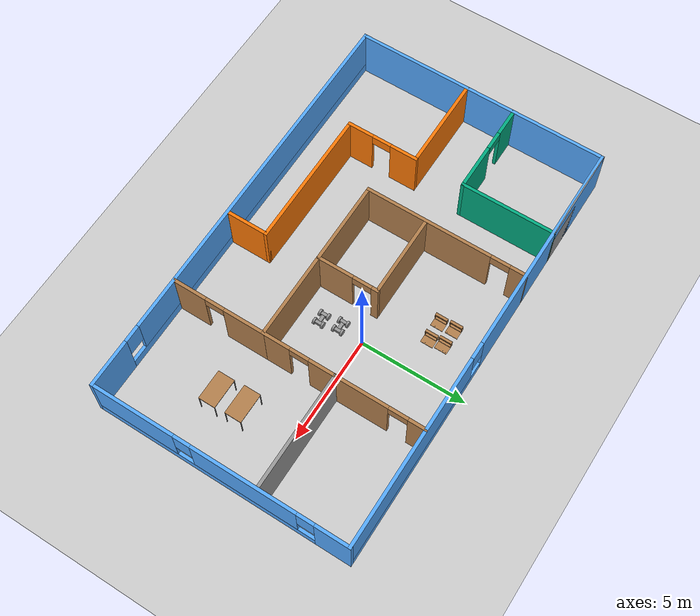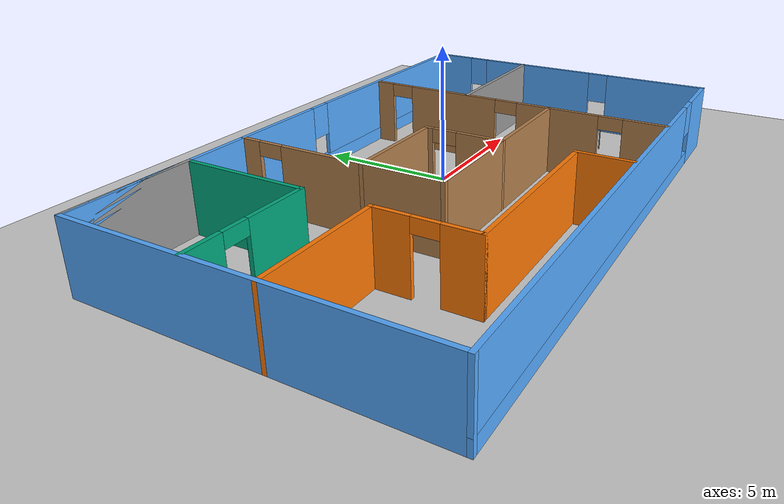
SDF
<sdf version="1.6">
 <world name="default">
  <plugin name="hello" filename="libwelcome.so"/>
  <light name="sun" type="directional">
   <pose>0 0 10 0 -0 0</pose>
   <diffuse>0.8 0.8 0.8 1</diffuse>
   <specular>0.1 0.1 0.1 1</specular>
   <attenuation>
    <range>1000</range>
    <constant>0.9</constant>
    <linear>0.01</linear>
    <quadratic>0.001</quadratic>
   </attenuation>
   <direction>-0.5 0.5 -1</direction>
  </light>
  <model name="ground_plane">
   <static>1</static>
   <link name="link">
    <collision name="collision">
     <geometry><plane><normal>0 0 1</normal><size>100 100</size></plane></geometry>
     <surface><friction><ode><mu>100</mu><mu2>50</mu2></ode></friction></surface>
    </collision>
    <visual name="visual">
     <cast_shadows>0</cast_shadows>
     <geometry><plane><normal>0 0 1</normal><size>100 100</size></plane></geometry>
     <material>
      <script><uri>file://media/materials/scripts/gazebo.material</uri><name>Gazebo/Grey</name></script>
     </material>
    </visual>
   </link>
  </model>
  <gravity>0 0 -9.8</gravity>
  <magnetic_field>6e-06 2.3e-05 -4.2e-05</magnetic_field>
  <atmosphere type="adiabatic"/>
  <physics name="default_physics" default="0" type="ode">
   <max_step_size>0.001</max_step_size>
   <real_time_factor>1</real_time_factor>
   <real_time_update_rate>1000</real_time_update_rate>
  </physics>
  <scene><ambient>0.4 0.4 0.4 1</ambient><background>0.7 0.7 0.7 1</background><shadows>1</shadows></scene>
  <spherical_coordinates>
   <surface_model>EARTH_WGS84</surface_model>
   <latitude_deg>0</latitude_deg>
   <longitude_deg>0</longitude_deg>
   <elevation>0</elevation>
   <heading_deg>0</heading_deg>
  </spherical_coordinates>
  <model name="robot">
   <link name="link_0">
    <pose>-0.225 0 0 0 -0 0</pose>
    <inertial>
     <mass>1</mass>
     <inertia>
      <ixx>0.166667</ixx>
      <ixy>0</ixy>
      <ixz>0</ixz>
      <iyy>0.166667</iyy>
      <iyz>0</iyz>
      <izz>0.166667</izz>
     </inertia>
    </inertial>
    <visual name="visual">
     <geometry><box><size>0.15 0.3 0.15</size></box></geometry>
     <material>
      <lighting>1</lighting>
      <script><uri>file://media/materials/scripts/gazebo.material</uri><name>Gazebo/Grey</name></script>
      <ambient>0.3 0.3 0.3 1</ambient>
      <diffuse>0.7 0.7 0.7 1</diffuse>
      <specular>0.01 0.01 0.01 1</specular>
      <emissive>0 0 0 1</emissive>
      <shader type="vertex"><normal_map>__default__</normal_map></shader>
     </material>
    </visual>
    <collision name="collision">
     <geometry><box><size>0.15 0.3 0.15</size></box></geometry>
     <surface>
      <friction>
       <ode><mu>1</mu><mu2>1</mu2><fdir1>0 0 0</fdir1><slip1>0</slip1><slip2>0</slip2></ode>
       <torsional>
        <coefficient>1</coefficient>
        <patch_radius>0</patch_radius>
        <surface_radius>0</surface_radius>
        <use_patch_radius>1</use_patch_radius>
        <ode><slip>0</slip></ode>
       </torsional>
      </friction>
      <bounce><restitution_coefficient>0</restitution_coefficient><threshold>1e+06</threshold></bounce>
      <contact>
       <collide_without_contact>0</collide_without_contact>
       <collide_without_contact_bitmask>1</collide_without_contact_bitmask>
       <collide_bitmask>1</collide_bitmask>
       <ode>
        <soft_cfm>0</soft_cfm>
        <soft_erp>0.2</soft_erp>
        <kp>1e+13</kp>
        <kd>1</kd>
        <max_vel>0.01</max_vel>
        <min_depth>0</min_depth>
       </ode>
       <bullet>
        <split_impulse>1</split_impulse>
        <split_impulse_penetration_threshold>-0.01</split_impulse_penetration_threshold>
        <soft_cfm>0</soft_cfm>
        <soft_erp>0.2</soft_erp>
        <kp>1e+13</kp>
        <kd>1</kd>
       </bullet>
      </contact>
     </surface>
    </collision>
   </link>
   <link name="link_0_clone">
    <pose>0.225 0 0 0 -0 0</pose>
    <inertial>
     <mass>1</mass>
     <inertia>
      <ixx>0.166667</ixx>
      <ixy>0</ixy>
      <ixz>0</ixz>
      <iyy>0.166667</iyy>
      <iyz>0</iyz>
      <izz>0.166667</izz>
     </inertia>
    </inertial>
    <visual name="visual">
     <geometry><box><size>0.15 0.3 0.15</size></box></geometry>
     <material>
      <lighting>1</lighting>
      <script><uri>file://media/materials/scripts/gazebo.material</uri><name>Gazebo/Grey</name></script>
      <ambient>0.3 0.3 0.3 1</ambient>
      <diffuse>0.7 0.7 0.7 1</diffuse>
      <specular>0.01 0.01 0.01 1</specular>
      <emissive>0 0 0 1</emissive>
      <shader type="vertex"><normal_map>__default__</normal_map></shader>
     </material>
    </visual>
    <collision name="collision">
     <geometry><box><size>0.15 0.3 0.15</size></box></geometry>
     <surface>
      <friction>
       <ode><mu>1</mu><mu2>1</mu2><fdir1>0 0 0</fdir1><slip1>0</slip1><slip2>0</slip2></ode>
       <torsional>
        <coefficient>1</coefficient>
        <patch_radius>0</patch_radius>
        <surface_radius>0</surface_radius>
        <use_patch_radius>1</use_patch_radius>
        <ode><slip>0</slip></ode>
       </torsional>
      </friction>
      <bounce><restitution_coefficient>0</restitution_coefficient><threshold>1e+06</threshold></bounce>
      <contact>
       <collide_without_contact>0</collide_without_contact>
       <collide_without_contact_bitmask>1</collide_without_contact_bitmask>
       <collide_bitmask>1</collide_bitmask>
       <ode>
        <soft_cfm>0</soft_cfm>
        <soft_erp>0.2</soft_erp>
        <kp>1e+13</kp>
        <kd>1</kd>
        <max_vel>0.01</max_vel>
        <min_depth>0</min_depth>
       </ode>
       <bullet>
        <split_impulse>1</split_impulse>
        <split_impulse_penetration_threshold>-0.01</split_impulse_penetration_threshold>
        <soft_cfm>0</soft_cfm>
        <soft_erp>0.2</soft_erp>
        <kp>1e+13</kp>
        <kd>1</kd>
       </bullet>
      </contact>
     </surface>
    </collision>
   </link>
   <link name="link_1">
    <inertial>
     <mass>1</mass>
     <inertia>
      <ixx>0.166667</ixx>
      <ixy>0</ixy>
      <ixz>0</ixz>
      <iyy>0.166667</iyy>
      <iyz>0</iyz>
      <izz>0.166667</izz>
     </inertia>
    </inertial>
    <visual name="visual">
     <geometry><box><size>0.3 0.15 0.15</size></box></geometry>
     <material>
      <lighting>1</lighting>
      <script><uri>file://media/materials/scripts/gazebo.material</uri><name>Gazebo/Grey</name></script>
      <ambient>0.3 0.3 0.3 1</ambient>
      <diffuse>0.7 0.7 0.7 1</diffuse>
      <specular>0.01 0.01 0.01 1</specular>
      <emissive>0 0 0 1</emissive>
      <shader type="vertex"><normal_map>__default__</normal_map></shader>
     </material>
    </visual>
    <collision name="collision">
     <geometry><box><size>0.3 0.15 0.15</size></box></geometry>
     <surface>
      <friction>
       <ode><mu>1</mu><mu2>1</mu2><fdir1>0 0 0</fdir1><slip1>0</slip1><slip2>0</slip2></ode>
       <torsional>
        <coefficient>1</coefficient>
        <patch_radius>0</patch_radius>
        <surface_radius>0</surface_radius>
        <use_patch_radius>1</use_patch_radius>
        <ode><slip>0</slip></ode>
       </torsional>
      </friction>
      <bounce><restitution_coefficient>0</restitution_coefficient><threshold>1e+06</threshold></bounce>
      <contact>
       <collide_without_contact>0</collide_without_contact>
       <collide_without_contact_bitmask>1</collide_without_contact_bitmask>
       <collide_bitmask>1</collide_bitmask>
       <ode>
        <soft_cfm>0</soft_cfm>
        <soft_erp>0.2</soft_erp>
        <kp>1e+13</kp>
        <kd>1</kd>
        <max_vel>0.01</max_vel>
        <min_depth>0</min_depth>
       </ode>
       <bullet>
        <split_impulse>1</split_impulse>
        <split_impulse_penetration_threshold>-0.01</split_impulse_penetration_threshold>
        <soft_cfm>0</soft_cfm>
        <soft_erp>0.2</soft_erp>
        <kp>1e+13</kp>
        <kd>1</kd>
       </bullet>
      </contact>
     </surface>
    </collision>
   </link>
   <link name="link_2">
    <pose>-0.225 -0.200001 0 1.5708 -0 0</pose>
    <inertial>
     <mass>1</mass>
     <inertia><ixx>0.145833</ixx><ixy>0</ixy><ixz>0</ixz><iyy>0.145833</iyy><iyz>0</iyz><izz>0.125</izz></inertia>
    </inertial>
    <visual name="visual">
     <geometry><cylinder><radius>0.15</radius><length>0.1</length></cylinder></geometry>
     <material>
      <lighting>1</lighting>
      <script><uri>file://media/materials/scripts/gazebo.material</uri><name>Gazebo/Grey</name></script>
      <ambient>0.3 0.3 0.3 1</ambient>
      <diffuse>0.7 0.7 0.7 1</diffuse>
      <specular>0.01 0.01 0.01 1</specular>
      <emissive>0 0 0 1</emissive>
      <shader type="vertex"><normal_map>__default__</normal_map></shader>
     </material>
    </visual>
    <collision name="collision">
     <geometry><cylinder><radius>0.15</radius><length>0.1</length></cylinder></geometry>
     <surface>
      <friction>
       <ode><mu>1</mu><mu2>1</mu2><fdir1>0 0 0</fdir1><slip1>0</slip1><slip2>0</slip2></ode>
       <torsional>
        <coefficient>1</coefficient>
        <patch_radius>0</patch_radius>
        <surface_radius>0</surface_radius>
        <use_patch_radius>1</use_patch_radius>
        <ode><slip>0</slip></ode>
       </torsional>
      </friction>
      <bounce><restitution_coefficient>0</restitution_coefficient><threshold>1e+06</threshold></bounce>
      <contact>
       <collide_without_contact>0</collide_without_contact>
       <collide_without_contact_bitmask>1</collide_without_contact_bitmask>
       <collide_bitmask>1</collide_bitmask>
       <ode>
        <soft_cfm>0</soft_cfm>
        <soft_erp>0.2</soft_erp>
        <kp>1e+13</kp>
        <kd>1</kd>
        <max_vel>0.01</max_vel>
        <min_depth>0</min_depth>
       </ode>
       <bullet>
        <split_impulse>1</split_impulse>
        <split_impulse_penetration_threshold>-0.01</split_impulse_penetration_threshold>
        <soft_cfm>0</soft_cfm>
        <soft_erp>0.2</soft_erp>
        <kp>1e+13</kp>
        <kd>1</kd>
       </bullet>
      </contact>
     </surface>
    </collision>
   </link>
   <link name="link_2_clone">
    <pose>0.225 -0.200001 0 1.5708 -0 0</pose>
    <inertial>
     <mass>1</mass>
     <inertia><ixx>0.145833</ixx><ixy>0</ixy><ixz>0</ixz><iyy>0.145833</iyy><iyz>0</iyz><izz>0.125</izz></inertia>
    </inertial>
    <visual name="visual">
     <geometry><cylinder><radius>0.15</radius><length>0.1</length></cylinder></geometry>
     <material>
      <lighting>1</lighting>
      <script><uri>file://media/materials/scripts/gazebo.material</uri><name>Gazebo/Grey</name></script>
      <ambient>0.3 0.3 0.3 1</ambient>
      <diffuse>0.7 0.7 0.7 1</diffuse>
      <specular>0.01 0.01 0.01 1</specular>
      <emissive>0 0 0 1</emissive>
      <shader type="vertex"><normal_map>__default__</normal_map></shader>
     </material>
    </visual>
    <collision name="collision">
     <geometry><cylinder><radius>0.15</radius><length>0.1</length></cylinder></geometry>
     <surface>
      <friction>
       <ode><mu>1</mu><mu2>1</mu2><fdir1>0 0 0</fdir1><slip1>0</slip1><slip2>0</slip2></ode>
       <torsional>
        <coefficient>1</coefficient>
        <patch_radius>0</patch_radius>
        <surface_radius>0</surface_radius>
        <use_patch_radius>1</use_patch_radius>
        <ode><slip>0</slip></ode>
       </torsional>
      </friction>
      <bounce><restitution_coefficient>0</restitution_coefficient><threshold>1e+06</threshold></bounce>
      <contact>
       <collide_without_contact>0</collide_without_contact>
       <collide_without_contact_bitmask>1</collide_without_contact_bitmask>
       <collide_bitmask>1</collide_bitmask>
       <ode>
        <soft_cfm>0</soft_cfm>
        <soft_erp>0.2</soft_erp>
        <kp>1e+13</kp>
        <kd>1</kd>
        <max_vel>0.01</max_vel>
        <min_depth>0</min_depth>
       </ode>
       <bullet>
        <split_impulse>1</split_impulse>
        <split_impulse_penetration_threshold>-0.01</split_impulse_penetration_threshold>
        <soft_cfm>0</soft_cfm>
        <soft_erp>0.2</soft_erp>
        <kp>1e+13</kp>
        <kd>1</kd>
       </bullet>
      </contact>
     </surface>
    </collision>
   </link>
   <link name="link_2_clone_0">
    <pose>-0.225 0.200001 0 1.5708 -0 0</pose>
    <inertial>
     <mass>1</mass>
     <inertia><ixx>0.145833</ixx><ixy>0</ixy><ixz>0</ixz><iyy>0.145833</iyy><iyz>0</iyz><izz>0.125</izz></inertia>
    </inertial>
    <visual name="visual">
     <geometry><cylinder><radius>0.15</radius><length>0.1</length></cylinder></geometry>
     <material>
      <lighting>1</lighting>
      <script><uri>file://media/materials/scripts/gazebo.material</uri><name>Gazebo/Grey</name></script>
      <ambient>0.3 0.3 0.3 1</ambient>
      <diffuse>0.7 0.7 0.7 1</diffuse>
      <specular>0.01 0.01 0.01 1</specular>
      <emissive>0 0 0 1</emissive>
      <shader type="vertex"><normal_map>__default__</normal_map></shader>
     </material>
    </visual>
    <collision name="collision">
     <geometry><cylinder><radius>0.15</radius><length>0.1</length></cylinder></geometry>
     <surface>
      <friction>
       <ode><mu>1</mu><mu2>1</mu2><fdir1>0 0 0</fdir1><slip1>0</slip1><slip2>0</slip2></ode>
       <torsional>
        <coefficient>1</coefficient>
        <patch_radius>0</patch_radius>
        <surface_radius>0</surface_radius>
        <use_patch_radius>1</use_patch_radius>
        <ode><slip>0</slip></ode>
       </torsional>
      </friction>
      <bounce><restitution_coefficient>0</restitution_coefficient><threshold>1e+06</threshold></bounce>
      <contact>
       <collide_without_contact>0</collide_without_contact>
       <collide_without_contact_bitmask>1</collide_without_contact_bitmask>
       <collide_bitmask>1</collide_bitmask>
       <ode>
        <soft_cfm>0</soft_cfm>
        <soft_erp>0.2</soft_erp>
        <kp>1e+13</kp>
        <kd>1</kd>
        <max_vel>0.01</max_vel>
        <min_depth>0</min_depth>
       </ode>
       <bullet>
        <split_impulse>1</split_impulse>
        <split_impulse_penetration_threshold>-0.01</split_impulse_penetration_threshold>
        <soft_cfm>0</soft_cfm>
        <soft_erp>0.2</soft_erp>
        <kp>1e+13</kp>
        <kd>1</kd>
       </bullet>
      </contact>
     </surface>
    </collision>
   </link>
   <link name="link_2_clone_1">
    <pose>0.225 0.200001 0 1.5708 -0 0</pose>
    <inertial>
     <mass>1</mass>
     <inertia><ixx>0.145833</ixx><ixy>0</ixy><ixz>0</ixz><iyy>0.145833</iyy><iyz>0</iyz><izz>0.125</izz></inertia>
    </inertial>
    <visual name="visual">
     <geometry><cylinder><radius>0.15</radius><length>0.1</length></cylinder></geometry>
     <material>
      <lighting>1</lighting>
      <script><uri>file://media/materials/scripts/gazebo.material</uri><name>Gazebo/Grey</name></script>
      <ambient>0.3 0.3 0.3 1</ambient>
      <diffuse>0.7 0.7 0.7 1</diffuse>
      <specular>0.01 0.01 0.01 1</specular>
      <emissive>0 0 0 1</emissive>
      <shader type="vertex"><normal_map>__default__</normal_map></shader>
     </material>
    </visual>
    <collision name="collision">
     <geometry><cylinder><radius>0.15</radius><length>0.1</length></cylinder></geometry>
     <surface>
      <friction>
       <ode><mu>1</mu><mu2>1</mu2><fdir1>0 0 0</fdir1><slip1>0</slip1><slip2>0</slip2></ode>
       <torsional>
        <coefficient>1</coefficient>
        <patch_radius>0</patch_radius>
        <surface_radius>0</surface_radius>
        <use_patch_radius>1</use_patch_radius>
        <ode><slip>0</slip></ode>
       </torsional>
      </friction>
      <bounce><restitution_coefficient>0</restitution_coefficient><threshold>1e+06</threshold></bounce>
      <contact>
       <collide_without_contact>0</collide_without_contact>
       <collide_without_contact_bitmask>1</collide_without_contact_bitmask>
       <collide_bitmask>1</collide_bitmask>
       <ode>
        <soft_cfm>0</soft_cfm>
        <soft_erp>0.2</soft_erp>
        <kp>1e+13</kp>
        <kd>1</kd>
        <max_vel>0.01</max_vel>
        <min_depth>0</min_depth>
       </ode>
       <bullet>
        <split_impulse>1</split_impulse>
        <split_impulse_penetration_threshold>-0.01</split_impulse_penetration_threshold>
        <soft_cfm>0</soft_cfm>
        <soft_erp>0.2</soft_erp>
        <kp>1e+13</kp>
        <kd>1</kd>
       </bullet>
      </contact>
     </surface>
    </collision>
   </link>
   <joint name="link_0_JOINT_1" type="fixed">
    <parent>link_0</parent>
    <child>link_1</child>
    <physics>
     <ode><limit><cfm>0</cfm><erp>0.2</erp></limit><suspension><cfm>0</cfm><erp>0.2</erp></suspension></ode>
    </physics>
   </joint>
   <joint name="link_0_JOINT_3" type="revolute">
    <parent>link_0</parent>
    <child>link_2</child>
    <axis>
     <xyz>1 0 0</xyz>
     <use_parent_model_frame>0</use_parent_model_frame>
     <limit>
      <lower>-1.79769e+308</lower>
      <upper>1.79769e+308</upper>
      <effort>-1</effort>
      <velocity>-1</velocity>
     </limit>
     <dynamics>
      <spring_reference>0</spring_reference>
      <spring_stiffness>0</spring_stiffness>
      <damping>0</damping>
     </dynamics>
    </axis>
    <physics>
     <ode><limit><cfm>0</cfm><erp>0.2</erp></limit><suspension><cfm>0</cfm><erp>0.2</erp></suspension></ode>
    </physics>
   </joint>
   <joint name="link_0_JOINT_5" type="revolute">
    <parent>link_0</parent>
    <child>link_2_clone_0</child>
    <axis>
     <xyz>1 0 0</xyz>
     <use_parent_model_frame>0</use_parent_model_frame>
     <limit>
      <lower>-1.79769e+308</lower>
      <upper>1.79769e+308</upper>
      <effort>-1</effort>
      <velocity>-1</velocity>
     </limit>
     <dynamics>
      <spring_reference>0</spring_reference>
      <spring_stiffness>0</spring_stiffness>
      <damping>0</damping>
     </dynamics>
    </axis>
    <physics>
     <ode><limit><cfm>0</cfm><erp>0.2</erp></limit><suspension><cfm>0</cfm><erp>0.2</erp></suspension></ode>
    </physics>
   </joint>
   <joint name="link_0_clone_JOINT_4" type="revolute">
    <parent>link_0_clone</parent>
    <child>link_2_clone</child>
    <axis>
     <xyz>1 0 0</xyz>
     <use_parent_model_frame>0</use_parent_model_frame>
     <limit>
      <lower>-1.79769e+308</lower>
      <upper>1.79769e+308</upper>
      <effort>-1</effort>
      <velocity>-1</velocity>
     </limit>
     <dynamics>
      <spring_reference>0</spring_reference>
      <spring_stiffness>0</spring_stiffness>
      <damping>0</damping>
     </dynamics>
    </axis>
    <physics>
     <ode><limit><cfm>0</cfm><erp>0.2</erp></limit><suspension><cfm>0</cfm><erp>0.2</erp></suspension></ode>
    </physics>
   </joint>
   <joint name="link_0_clone_JOINT_6" type="revolute">
    <parent>link_0_clone</parent>
    <child>link_2_clone_1</child>
    <axis>
     <xyz>1 0 0</xyz>
     <use_parent_model_frame>0</use_parent_model_frame>
     <limit>
      <lower>-1.79769e+308</lower>
      <upper>1.79769e+308</upper>
      <effort>-1</effort>
      <velocity>-1</velocity>
     </limit>
     <dynamics>
      <spring_reference>0</spring_reference>
      <spring_stiffness>0</spring_stiffness>
      <damping>0</damping>
     </dynamics>
    </axis>
    <physics>
     <ode><limit><cfm>0</cfm><erp>0.2</erp></limit><suspension><cfm>0</cfm><erp>0.2</erp></suspension></ode>
    </physics>
   </joint>
   <joint name="link_1_JOINT_2" type="fixed">
    <parent>link_1</parent>
    <child>link_0_clone</child>
    <physics>
     <ode><limit><cfm>0</cfm><erp>0.2</erp></limit><suspension><cfm>0</cfm><erp>0.2</erp></suspension></ode>
    </physics>
   </joint>
   <static>0</static>
   <pose>0.033407 -2.00112 0.15 0 0 -0.000604</pose>
  </model>
  <model name="robot_0">
   <link name="link_0">
    <pose>-0.225 0 0 0 -0 0</pose>
    <inertial>
     <mass>1</mass>
     <inertia>
      <ixx>0.166667</ixx>
      <ixy>0</ixy>
      <ixz>0</ixz>
      <iyy>0.166667</iyy>
      <iyz>0</iyz>
      <izz>0.166667</izz>
     </inertia>
    </inertial>
    <visual name="visual">
     <geometry><box><size>0.15 0.3 0.15</size></box></geometry>
     <material>
      <lighting>1</lighting>
      <script><uri>file://media/materials/scripts/gazebo.material</uri><name>Gazebo/Grey</name></script>
      <ambient>0.3 0.3 0.3 1</ambient>
      <diffuse>0.7 0.7 0.7 1</diffuse>
      <specular>0.01 0.01 0.01 1</specular>
      <emissive>0 0 0 1</emissive>
      <shader type="vertex"><normal_map>__default__</normal_map></shader>
     </material>
    </visual>
    <collision name="collision">
     <geometry><box><size>0.15 0.3 0.15</size></box></geometry>
     <surface>
      <friction>
       <ode><mu>1</mu><mu2>1</mu2><fdir1>0 0 0</fdir1><slip1>0</slip1><slip2>0</slip2></ode>
       <torsional>
        <coefficient>1</coefficient>
        <patch_radius>0</patch_radius>
        <surface_radius>0</surface_radius>
        <use_patch_radius>1</use_patch_radius>
        <ode><slip>0</slip></ode>
       </torsional>
      </friction>
      <bounce><restitution_coefficient>0</restitution_coefficient><threshold>1e+06</threshold></bounce>
      <contact>
       <collide_without_contact>0</collide_without_contact>
       <collide_without_contact_bitmask>1</collide_without_contact_bitmask>
       <collide_bitmask>1</collide_bitmask>
       <ode>
        <soft_cfm>0</soft_cfm>
        <soft_erp>0.2</soft_erp>
        <kp>1e+13</kp>
        <kd>1</kd>
        <max_vel>0.01</max_vel>
        <min_depth>0</min_depth>
       </ode>
       <bullet>
        <split_impulse>1</split_impulse>
        <split_impulse_penetration_threshold>-0.01</split_impulse_penetration_threshold>
        <soft_cfm>0</soft_cfm>
        <soft_erp>0.2</soft_erp>
        <kp>1e+13</kp>
        <kd>1</kd>
       </bullet>
      </contact>
     </surface>
    </collision>
   </link>
   <link name="link_0_clone">
    <pose>0.225 0 0 0 -0 0</pose>
    <inertial>
     <mass>1</mass>
     <inertia>
      <ixx>0.166667</ixx>
      <ixy>0</ixy>
      <ixz>0</ixz>
      <iyy>0.166667</iyy>
      <iyz>0</iyz>
      <izz>0.166667</izz>
     </inertia>
    </inertial>
    <visual name="visual">
     <geometry><box><size>0.15 0.3 0.15</size></box></geometry>
     <material>
      <lighting>1</lighting>
      <script><uri>file://media/materials/scripts/gazebo.material</uri><name>Gazebo/Grey</name></script>
      <ambient>0.3 0.3 0.3 1</ambient>
      <diffuse>0.7 0.7 0.7 1</diffuse>
      <specular>0.01 0.01 0.01 1</specular>
      <emissive>0 0 0 1</emissive>
      <shader type="vertex"><normal_map>__default__</normal_map></shader>
     </material>
    </visual>
    <collision name="collision">
     <geometry><box><size>0.15 0.3 0.15</size></box></geometry>
     <surface>
      <friction>
       <ode><mu>1</mu><mu2>1</mu2><fdir1>0 0 0</fdir1><slip1>0</slip1><slip2>0</slip2></ode>
       <torsional>
        <coefficient>1</coefficient>
        <patch_radius>0</patch_radius>
        <surface_radius>0</surface_radius>
        <use_patch_radius>1</use_patch_radius>
        <ode><slip>0</slip></ode>
       </torsional>
      </friction>
      <bounce><restitution_coefficient>0</restitution_coefficient><threshold>1e+06</threshold></bounce>
      <contact>
       <collide_without_contact>0</collide_without_contact>
       <collide_without_contact_bitmask>1</collide_without_contact_bitmask>
       <collide_bitmask>1</collide_bitmask>
       <ode>
        <soft_cfm>0</soft_cfm>
        <soft_erp>0.2</soft_erp>
        <kp>1e+13</kp>
        <kd>1</kd>
        <max_vel>0.01</max_vel>
        <min_depth>0</min_depth>
       </ode>
       <bullet>
        <split_impulse>1</split_impulse>
        <split_impulse_penetration_threshold>-0.01</split_impulse_penetration_threshold>
        <soft_cfm>0</soft_cfm>
        <soft_erp>0.2</soft_erp>
        <kp>1e+13</kp>
        <kd>1</kd>
       </bullet>
      </contact>
     </surface>
    </collision>
   </link>
   <link name="link_1">
    <inertial>
     <mass>1</mass>
     <inertia>
      <ixx>0.166667</ixx>
      <ixy>0</ixy>
      <ixz>0</ixz>
      <iyy>0.166667</iyy>
      <iyz>0</iyz>
      <izz>0.166667</izz>
     </inertia>
    </inertial>
    <visual name="visual">
     <geometry><box><size>0.3 0.15 0.15</size></box></geometry>
     <material>
      <lighting>1</lighting>
      <script><uri>file://media/materials/scripts/gazebo.material</uri><name>Gazebo/Grey</name></script>
      <ambient>0.3 0.3 0.3 1</ambient>
      <diffuse>0.7 0.7 0.7 1</diffuse>
      <specular>0.01 0.01 0.01 1</specular>
      <emissive>0 0 0 1</emissive>
      <shader type="vertex"><normal_map>__default__</normal_map></shader>
     </material>
    </visual>
    <collision name="collision">
     <geometry><box><size>0.3 0.15 0.15</size></box></geometry>
     <surface>
      <friction>
       <ode><mu>1</mu><mu2>1</mu2><fdir1>0 0 0</fdir1><slip1>0</slip1><slip2>0</slip2></ode>
       <torsional>
        <coefficient>1</coefficient>
        <patch_radius>0</patch_radius>
        <surface_radius>0</surface_radius>
        <use_patch_radius>1</use_patch_radius>
        <ode><slip>0</slip></ode>
       </torsional>
      </friction>
      <bounce><restitution_coefficient>0</restitution_coefficient><threshold>1e+06</threshold></bounce>
      <contact>
       <collide_without_contact>0</collide_without_contact>
       <collide_without_contact_bitmask>1</collide_without_contact_bitmask>
       <collide_bitmask>1</collide_bitmask>
       <ode>
        <soft_cfm>0</soft_cfm>
        <soft_erp>0.2</soft_erp>
        <kp>1e+13</kp>
        <kd>1</kd>
        <max_vel>0.01</max_vel>
        <min_depth>0</min_depth>
       </ode>
       <bullet>
        <split_impulse>1</split_impulse>
        <split_impulse_penetration_threshold>-0.01</split_impulse_penetration_threshold>
        <soft_cfm>0</soft_cfm>
        <soft_erp>0.2</soft_erp>
        <kp>1e+13</kp>
        <kd>1</kd>
       </bullet>
      </contact>
     </surface>
    </collision>
   </link>
   <link name="link_2">
    <pose>-0.225 -0.200001 0 1.5708 -0 0</pose>
    <inertial>
     <mass>1</mass>
     <inertia><ixx>0.145833</ixx><ixy>0</ixy><ixz>0</ixz><iyy>0.145833</iyy><iyz>0</iyz><izz>0.125</izz></inertia>
    </inertial>
    <visual name="visual">
     <geometry><cylinder><radius>0.15</radius><length>0.1</length></cylinder></geometry>
     <material>
      <lighting>1</lighting>
      <script><uri>file://media/materials/scripts/gazebo.material</uri><name>Gazebo/Grey</name></script>
      <ambient>0.3 0.3 0.3 1</ambient>
      <diffuse>0.7 0.7 0.7 1</diffuse>
      <specular>0.01 0.01 0.01 1</specular>
      <emissive>0 0 0 1</emissive>
      <shader type="vertex"><normal_map>__default__</normal_map></shader>
     </material>
    </visual>
    <collision name="collision">
     <geometry><cylinder><radius>0.15</radius><length>0.1</length></cylinder></geometry>
     <surface>
      <friction>
       <ode><mu>1</mu><mu2>1</mu2><fdir1>0 0 0</fdir1><slip1>0</slip1><slip2>0</slip2></ode>
       <torsional>
        <coefficient>1</coefficient>
        <patch_radius>0</patch_radius>
        <surface_radius>0</surface_radius>
        <use_patch_radius>1</use_patch_radius>
        <ode><slip>0</slip></ode>
       </torsional>
      </friction>
      <bounce><restitution_coefficient>0</restitution_coefficient><threshold>1e+06</threshold></bounce>
      <contact>
       <collide_without_contact>0</collide_without_contact>
       <collide_without_contact_bitmask>1</collide_without_contact_bitmask>
       <collide_bitmask>1</collide_bitmask>
       <ode>
        <soft_cfm>0</soft_cfm>
        <soft_erp>0.2</soft_erp>
        <kp>1e+13</kp>
        <kd>1</kd>
        <max_vel>0.01</max_vel>
        <min_depth>0</min_depth>
       </ode>
       <bullet>
        <split_impulse>1</split_impulse>
        <split_impulse_penetration_threshold>-0.01</split_impulse_penetration_threshold>
        <soft_cfm>0</soft_cfm>
        <soft_erp>0.2</soft_erp>
        <kp>1e+13</kp>
        <kd>1</kd>
       </bullet>
      </contact>
     </surface>
    </collision>
   </link>
   <link name="link_2_clone">
    <pose>0.225 -0.200001 0 1.5708 -0 0</pose>
    <inertial>
     <mass>1</mass>
     <inertia><ixx>0.145833</ixx><ixy>0</ixy><ixz>0</ixz><iyy>0.145833</iyy><iyz>0</iyz><izz>0.125</izz></inertia>
    </inertial>
    <visual name="visual">
     <geometry><cylinder><radius>0.15</radius><length>0.1</length></cylinder></geometry>
     <material>
      <lighting>1</lighting>
      <script><uri>file://media/materials/scripts/gazebo.material</uri><name>Gazebo/Grey</name></script>
      <ambient>0.3 0.3 0.3 1</ambient>
      <diffuse>0.7 0.7 0.7 1</diffuse>
      <specular>0.01 0.01 0.01 1</specular>
      <emissive>0 0 0 1</emissive>
      <shader type="vertex"><normal_map>__default__</normal_map></shader>
     </material>
    </visual>
    <collision name="collision">
     <geometry><cylinder><radius>0.15</radius><length>0.1</length></cylinder></geometry>
     <surface>
      <friction>
       <ode><mu>1</mu><mu2>1</mu2><fdir1>0 0 0</fdir1><slip1>0</slip1><slip2>0</slip2></ode>
       <torsional>
        <coefficient>1</coefficient>
        <patch_radius>0</patch_radius>
        <surface_radius>0</surface_radius>
        <use_patch_radius>1</use_patch_radius>
        <ode><slip>0</slip></ode>
       </torsional>
      </friction>
      <bounce><restitution_coefficient>0</restitution_coefficient><threshold>1e+06</threshold></bounce>
      <contact>
       <collide_without_contact>0</collide_without_contact>
       <collide_without_contact_bitmask>1</collide_without_contact_bitmask>
       <collide_bitmask>1</collide_bitmask>
       <ode>
        <soft_cfm>0</soft_cfm>
        <soft_erp>0.2</soft_erp>
        <kp>1e+13</kp>
        <kd>1</kd>
        <max_vel>0.01</max_vel>
        <min_depth>0</min_depth>
       </ode>
       <bullet>
        <split_impulse>1</split_impulse>
        <split_impulse_penetration_threshold>-0.01</split_impulse_penetration_threshold>
        <soft_cfm>0</soft_cfm>
        <soft_erp>0.2</soft_erp>
        <kp>1e+13</kp>
        <kd>1</kd>
       </bullet>
      </contact>
     </surface>
    </collision>
   </link>
   <link name="link_2_clone_0">
    <pose>-0.225 0.200001 0 1.5708 -0 0</pose>
    <inertial>
     <mass>1</mass>
     <inertia><ixx>0.145833</ixx><ixy>0</ixy><ixz>0</ixz><iyy>0.145833</iyy><iyz>0</iyz><izz>0.125</izz></inertia>
    </inertial>
    <visual name="visual">
     <geometry><cylinder><radius>0.15</radius><length>0.1</length></cylinder></geometry>
     <material>
      <lighting>1</lighting>
      <script><uri>file://media/materials/scripts/gazebo.material</uri><name>Gazebo/Grey</name></script>
      <ambient>0.3 0.3 0.3 1</ambient>
      <diffuse>0.7 0.7 0.7 1</diffuse>
      <specular>0.01 0.01 0.01 1</specular>
      <emissive>0 0 0 1</emissive>
      <shader type="vertex"><normal_map>__default__</normal_map></shader>
     </material>
    </visual>
    <collision name="collision">
     <geometry><cylinder><radius>0.15</radius><length>0.1</length></cylinder></geometry>
     <surface>
      <friction>
       <ode><mu>1</mu><mu2>1</mu2><fdir1>0 0 0</fdir1><slip1>0</slip1><slip2>0</slip2></ode>
       <torsional>
        <coefficient>1</coefficient>
        <patch_radius>0</patch_radius>
        <surface_radius>0</surface_radius>
        <use_patch_radius>1</use_patch_radius>
        <ode><slip>0</slip></ode>
       </torsional>
      </friction>
      <bounce><restitution_coefficient>0</restitution_coefficient><threshold>1e+06</threshold></bounce>
      <contact>
       <collide_without_contact>0</collide_without_contact>
       <collide_without_contact_bitmask>1</collide_without_contact_bitmask>
       <collide_bitmask>1</collide_bitmask>
       <ode>
        <soft_cfm>0</soft_cfm>
        <soft_erp>0.2</soft_erp>
        <kp>1e+13</kp>
        <kd>1</kd>
        <max_vel>0.01</max_vel>
        <min_depth>0</min_depth>
       </ode>
       <bullet>
        <split_impulse>1</split_impulse>
        <split_impulse_penetration_threshold>-0.01</split_impulse_penetration_threshold>
        <soft_cfm>0</soft_cfm>
        <soft_erp>0.2</soft_erp>
        <kp>1e+13</kp>
        <kd>1</kd>
       </bullet>
      </contact>
     </surface>
    </collision>
   </link>
   <link name="link_2_clone_1">
    <pose>0.225 0.200001 0 1.5708 -0 0</pose>
    <inertial>
     <mass>1</mass>
     <inertia><ixx>0.145833</ixx><ixy>0</ixy><ixz>0</ixz><iyy>0.145833</iyy><iyz>0</iyz><izz>0.125</izz></inertia>
    </inertial>
    <visual name="visual">
     <geometry><cylinder><radius>0.15</radius><length>0.1</length></cylinder></geometry>
     <material>
      <lighting>1</lighting>
      <script><uri>file://media/materials/scripts/gazebo.material</uri><name>Gazebo/Grey</name></script>
      <ambient>0.3 0.3 0.3 1</ambient>
      <diffuse>0.7 0.7 0.7 1</diffuse>
      <specular>0.01 0.01 0.01 1</specular>
      <emissive>0 0 0 1</emissive>
      <shader type="vertex"><normal_map>__default__</normal_map></shader>
     </material>
    </visual>
    <collision name="collision">
     <geometry><cylinder><radius>0.15</radius><length>0.1</length></cylinder></geometry>
     <surface>
      <friction>
       <ode><mu>1</mu><mu2>1</mu2><fdir1>0 0 0</fdir1><slip1>0</slip1><slip2>0</slip2></ode>
       <torsional>
        <coefficient>1</coefficient>
        <patch_radius>0</patch_radius>
        <surface_radius>0</surface_radius>
        <use_patch_radius>1</use_patch_radius>
        <ode><slip>0</slip></ode>
       </torsional>
      </friction>
      <bounce><restitution_coefficient>0</restitution_coefficient><threshold>1e+06</threshold></bounce>
      <contact>
       <collide_without_contact>0</collide_without_contact>
       <collide_without_contact_bitmask>1</collide_without_contact_bitmask>
       <collide_bitmask>1</collide_bitmask>
       <ode>
        <soft_cfm>0</soft_cfm>
        <soft_erp>0.2</soft_erp>
        <kp>1e+13</kp>
        <kd>1</kd>
        <max_vel>0.01</max_vel>
        <min_depth>0</min_depth>
       </ode>
       <bullet>
        <split_impulse>1</split_impulse>
        <split_impulse_penetration_threshold>-0.01</split_impulse_penetration_threshold>
        <soft_cfm>0</soft_cfm>
        <soft_erp>0.2</soft_erp>
        <kp>1e+13</kp>
        <kd>1</kd>
       </bullet>
      </contact>
     </surface>
    </collision>
   </link>
   <joint name="link_0_JOINT_1" type="fixed">
    <parent>link_0</parent>
    <child>link_1</child>
    <physics>
     <ode><limit><cfm>0</cfm><erp>0.2</erp></limit><suspension><cfm>0</cfm><erp>0.2</erp></suspension></ode>
    </physics>
   </joint>
   <joint name="link_0_JOINT_3" type="revolute">
    <parent>link_0</parent>
    <child>link_2</child>
    <axis>
     <xyz>1 0 0</xyz>
     <use_parent_model_frame>0</use_parent_model_frame>
     <limit>
      <lower>-1.79769e+308</lower>
      <upper>1.79769e+308</upper>
      <effort>-1</effort>
      <velocity>-1</velocity>
     </limit>
     <dynamics>
      <spring_reference>0</spring_reference>
      <spring_stiffness>0</spring_stiffness>
      <damping>0</damping>
     </dynamics>
    </axis>
    <physics>
     <ode><limit><cfm>0</cfm><erp>0.2</erp></limit><suspension><cfm>0</cfm><erp>0.2</erp></suspension></ode>
    </physics>
   </joint>
   <joint name="link_0_JOINT_5" type="revolute">
    <parent>link_0</parent>
    <child>link_2_clone_0</child>
    <axis>
     <xyz>1 0 0</xyz>
     <use_parent_model_frame>0</use_parent_model_frame>
     <limit>
      <lower>-1.79769e+308</lower>
      <upper>1.79769e+308</upper>
      <effort>-1</effort>
      <velocity>-1</velocity>
     </limit>
     <dynamics>
      <spring_reference>0</spring_reference>
      <spring_stiffness>0</spring_stiffness>
      <damping>0</damping>
     </dynamics>
    </axis>
    <physics>
     <ode><limit><cfm>0</cfm><erp>0.2</erp></limit><suspension><cfm>0</cfm><erp>0.2</erp></suspension></ode>
    </physics>
   </joint>
   <joint name="link_0_clone_JOINT_4" type="revolute">
    <parent>link_0_clone</parent>
    <child>link_2_clone</child>
    <axis>
     <xyz>1 0 0</xyz>
     <use_parent_model_frame>0</use_parent_model_frame>
     <limit>
      <lower>-1.79769e+308</lower>
      <upper>1.79769e+308</upper>
      <effort>-1</effort>
      <velocity>-1</velocity>
     </limit>
     <dynamics>
      <spring_reference>0</spring_reference>
      <spring_stiffness>0</spring_stiffness>
      <damping>0</damping>
     </dynamics>
    </axis>
    <physics>
     <ode><limit><cfm>0</cfm><erp>0.2</erp></limit><suspension><cfm>0</cfm><erp>0.2</erp></suspension></ode>
    </physics>
   </joint>
   <joint name="link_0_clone_JOINT_6" type="revolute">
    <parent>link_0_clone</parent>
    <child>link_2_clone_1</child>
    <axis>
     <xyz>1 0 0</xyz>
     <use_parent_model_frame>0</use_parent_model_frame>
     <limit>
      <lower>-1.79769e+308</lower>
      <upper>1.79769e+308</upper>
      <effort>-1</effort>
      <velocity>-1</velocity>
     </limit>
     <dynamics>
      <spring_reference>0</spring_reference>
      <spring_stiffness>0</spring_stiffness>
      <damping>0</damping>
     </dynamics>
    </axis>
    <physics>
     <ode><limit><cfm>0</cfm><erp>0.2</erp></limit><suspension><cfm>0</cfm><erp>0.2</erp></suspension></ode>
    </physics>
   </joint>
   <joint name="link_1_JOINT_2" type="fixed">
    <parent>link_1</parent>
    <child>link_0_clone</child>
    <physics>
     <ode><limit><cfm>0</cfm><erp>0.2</erp></limit><suspension><cfm>0</cfm><erp>0.2</erp></suspension></ode>
    </physics>
   </joint>
   <static>0</static>
   <pose>-0.112792 -1.13248 0.15 0 -1e-06 -0.000535</pose>
  </model>
  <model name="office">
   <pose>-1.90978 -1.39181 0 0 -0 0</pose>
   <link name="Wall_22">
    <pose>0 6 0 0 -0 0</pose>
    <visual name="Wall_22_Visual_0">
     <pose>-4.91103 0 1.25 0 -0 0</pose>
     <geometry><box><size>10.3279 0.15 2.5</size></box></geometry>
     <material>
      <script><uri>file://media/materials/scripts/gazebo.material</uri><name>Gazebo/Grey</name></script>
      <ambient>0.333333 0.666667 1 1</ambient>
     </material>
    </visual>
    <collision name="Wall_22_Collision_0">
     <geometry><box><size>10.3279 0.15 2.5</size></box></geometry>
     <pose>-4.91103 0 1.25 0 -0 0</pose>
    </collision>
    <visual name="Wall_22_Visual_1">
     <pose>5.16397 0 0.25 0 -0 0</pose>
     <geometry><box><size>9.82205 0.15 0.5</size></box></geometry>
     <material>
      <script><uri>file://media/materials/scripts/gazebo.material</uri><name>Gazebo/Grey</name></script>
      <ambient>0.333333 0.666667 1 1</ambient>
     </material>
    </visual>
    <collision name="Wall_22_Collision_1">
     <geometry><box><size>9.82205 0.15 0.5</size></box></geometry>
     <pose>5.16397 0 0.25 0 -0 0</pose>
    </collision>
    <visual name="Wall_22_Visual_2">
     <pose>5.56397 0 1.5 0 -0 0</pose>
     <geometry><box><size>9.02205 0.15 2</size></box></geometry>
     <material>
      <script><uri>file://media/materials/scripts/gazebo.material</uri><name>Gazebo/Grey</name></script>
      <ambient>0.333333 0.666667 1 1</ambient>
     </material>
    </visual>
    <collision name="Wall_22_Collision_2">
     <geometry><box><size>9.02205 0.15 2</size></box></geometry>
     <pose>5.56397 0 1.5 0 -0 0</pose>
    </collision>
    <visual name="Wall_22_Visual_3">
     <pose>0.652946 0 1.9 0 -0 0</pose>
     <geometry><box><size>0.8 0.15 1.2</size></box></geometry>
     <material>
      <script><uri>file://media/materials/scripts/gazebo.material</uri><name>Gazebo/Grey</name></script>
      <ambient>0.333333 0.666667 1 1</ambient>
     </material>
    </visual>
    <collision name="Wall_22_Collision_3">
     <geometry><box><size>0.8 0.15 1.2</size></box></geometry>
     <pose>0.652946 0 1.9 0 -0 0</pose>
    </collision>
   </link>
   <link name="Wall_23">
    <pose>10 0 0 0 0 -1.5708</pose>
    <visual name="Wall_23_Visual_0">
     <pose>-5.24954 0 1.25 0 -0 0</pose>
     <geometry><box><size>1.65093 0.15 2.5</size></box></geometry>
     <material>
      <script><uri>file://media/materials/scripts/gazebo.material</uri><name>Gazebo/Grey</name></script>
      <ambient>0.333333 0.666667 1 1</ambient>
     </material>
    </visual>
    <collision name="Wall_23_Collision_0">
     <geometry><box><size>1.65093 0.15 2.5</size></box></geometry>
     <pose>-5.24954 0 1.25 0 -0 0</pose>
    </collision>
    <visual name="Wall_23_Visual_1">
     <pose>0.825463 0 0.25 0 -0 0</pose>
     <geometry><box><size>10.4991 0.15 0.5</size></box></geometry>
     <material>
      <script><uri>file://media/materials/scripts/gazebo.material</uri><name>Gazebo/Grey</name></script>
      <ambient>0.333333 0.666667 1 1</ambient>
     </material>
    </visual>
    <collision name="Wall_23_Collision_1">
     <geometry><box><size>10.4991 0.15 0.5</size></box></geometry>
     <pose>0.825463 0 0.25 0 -0 0</pose>
    </collision>
    <visual name="Wall_23_Visual_2">
     <pose>-1.17459 0 1.5 0 -0 0</pose>
     <geometry><box><size>4.89896 0.15 2</size></box></geometry>
     <material>
      <script><uri>file://media/materials/scripts/gazebo.material</uri><name>Gazebo/Grey</name></script>
      <ambient>0.333333 0.666667 1 1</ambient>
     </material>
    </visual>
    <collision name="Wall_23_Collision_2">
     <geometry><box><size>4.89896 0.15 2</size></box></geometry>
     <pose>-1.17459 0 1.5 0 -0 0</pose>
    </collision>
    <visual name="Wall_23_Visual_3">
     <pose>4.07494 0 1.5 0 -0 0</pose>
     <geometry><box><size>4.00011 0.15 2</size></box></geometry>
     <material>
      <script><uri>file://media/materials/scripts/gazebo.material</uri><name>Gazebo/Grey</name></script>
      <ambient>0.333333 0.666667 1 1</ambient>
     </material>
    </visual>
    <collision name="Wall_23_Collision_3">
     <geometry><box><size>4.00011 0.15 2</size></box></geometry>
     <pose>4.07494 0 1.5 0 -0 0</pose>
    </collision>
    <visual name="Wall_23_Visual_4">
     <pose>-4.02407 0 1.9 0 -0 0</pose>
     <geometry><box><size>0.8 0.15 1.2</size></box></geometry>
     <material>
      <script><uri>file://media/materials/scripts/gazebo.material</uri><name>Gazebo/Grey</name></script>
      <ambient>0.333333 0.666667 1 1</ambient>
     </material>
    </visual>
    <collision name="Wall_23_Collision_4">
     <geometry><box><size>0.8 0.15 1.2</size></box></geometry>
     <pose>-4.02407 0 1.9 0 -0 0</pose>
    </collision>
    <visual name="Wall_23_Visual_5">
     <pose>1.67489 0 1.9 0 -0 0</pose>
     <geometry><box><size>0.8 0.15 1.2</size></box></geometry>
     <material>
      <script><uri>file://media/materials/scripts/gazebo.material</uri><name>Gazebo/Grey</name></script>
      <ambient>0.333333 0.666667 1 1</ambient>
     </material>
    </visual>
    <collision name="Wall_23_Collision_5">
     <geometry><box><size>0.8 0.15 1.2</size></box></geometry>
     <pose>1.67489 0 1.9 0 -0 0</pose>
    </collision>
   </link>
   <link name="Wall_24">
    <pose>0 -6 0 0 -0 3.14159</pose>
    <visual name="Wall_24_Visual_0">
     <pose>-8.94993 0 1.25 0 -0 0</pose>
     <geometry><box><size>2.25014 0.15 2.5</size></box></geometry>
     <material>
      <script><uri>file://media/materials/scripts/gazebo.material</uri><name>Gazebo/Grey</name></script>
      <ambient>0.333333 0.666667 1 1</ambient>
     </material>
    </visual>
    <collision name="Wall_24_Collision_0">
     <geometry><box><size>2.25014 0.15 2.5</size></box></geometry>
     <pose>-8.94993 0 1.25 0 -0 0</pose>
    </collision>
    <visual name="Wall_24_Visual_1">
     <pose>1.12507 0 0.25 0 -0 0</pose>
     <geometry><box><size>17.8999 0.15 0.5</size></box></geometry>
     <material>
      <script><uri>file://media/materials/scripts/gazebo.material</uri><name>Gazebo/Grey</name></script>
      <ambient>0.333333 0.666667 1 1</ambient>
     </material>
    </visual>
    <collision name="Wall_24_Collision_1">
     <geometry><box><size>17.8999 0.15 0.5</size></box></geometry>
     <pose>1.12507 0 0.25 0 -0 0</pose>
    </collision>
    <visual name="Wall_24_Visual_2">
     <pose>1.52507 0 1.5 0 -0 0</pose>
     <geometry><box><size>17.0999 0.15 2</size></box></geometry>
     <material>
      <script><uri>file://media/materials/scripts/gazebo.material</uri><name>Gazebo/Grey</name></script>
      <ambient>0.333333 0.666667 1 1</ambient>
     </material>
    </visual>
    <collision name="Wall_24_Collision_2">
     <geometry><box><size>17.0999 0.15 2</size></box></geometry>
     <pose>1.52507 0 1.5 0 -0 0</pose>
    </collision>
    <visual name="Wall_24_Visual_3">
     <pose>-7.42486 0 1.9 0 -0 0</pose>
     <geometry><box><size>0.8 0.15 1.2</size></box></geometry>
     <material>
      <script><uri>file://media/materials/scripts/gazebo.material</uri><name>Gazebo/Grey</name></script>
      <ambient>0.333333 0.666667 1 1</ambient>
     </material>
    </visual>
    <collision name="Wall_24_Collision_3">
     <geometry><box><size>0.8 0.15 1.2</size></box></geometry>
     <pose>-7.42486 0 1.9 0 -0 0</pose>
    </collision>
   </link>
   <link name="Wall_25">
    <collision name="Wall_25_Collision">
     <geometry><box><size>12.15 0.15 2.5</size></box></geometry>
     <pose>0 0 1.25 0 -0 0</pose>
    </collision>
    <visual name="Wall_25_Visual">
     <pose>0 0 1.25 0 -0 0</pose>
     <geometry><box><size>12.15 0.15 2.5</size></box></geometry>
     <material>
      <script><uri>file://media/materials/scripts/gazebo.material</uri><name>Gazebo/Grey</name></script>
      <ambient>0.333333 0.666667 1 1</ambient>
     </material>
    </visual>
    <pose>-10 0 0 0 -0 1.5708</pose>
   </link>
   <link name="Wall_29">
    <collision name="Wall_29_Collision">
     <geometry><box><size>4.5 0.15 2.5</size></box></geometry>
     <pose>0 0 1.25 0 -0 0</pose>
    </collision>
    <visual name="Wall_29_Visual">
     <pose>0 0 1.25 0 -0 0</pose>
     <geometry><box><size>4.5 0.15 2.5</size></box></geometry>
     <material>
      <script><uri>file://media/materials/scripts/gazebo.material</uri><name>Gazebo/Grey</name></script>
      <ambient>1 1 1 1</ambient>
     </material>
    </visual>
    <pose>-7.825 6 0 0 -0 0</pose>
   </link>
   <link name="Wall_30">
    <collision name="Wall_30_Collision">
     <geometry><box><size>4.5 0.15 2.5</size></box></geometry>
     <pose>0 0 1.25 0 -0 0</pose>
    </collision>
    <visual name="Wall_30_Visual">
     <pose>0 0 1.25 0 -0 0</pose>
     <geometry><box><size>4.5 0.15 2.5</size></box></geometry>
     <material>
      <script><uri>file://media/materials/scripts/gazebo.material</uri><name>Gazebo/Grey</name></script>
      <ambient>0 0.666667 0.498039 1</ambient>
     </material>
    </visual>
    <pose>-5.65 3.825 0 0 0 -1.5708</pose>
   </link>
   <link name="Wall_31">
    <pose>-7.825 1.65 0 0 -0 3.14159</pose>
    <visual name="Wall_31_Visual_0">
     <pose>-1.13886 0 1.25 0 -0 0</pose>
     <geometry><box><size>2.22228 0.15 2.5</size></box></geometry>
     <material>
      <script><uri>file://media/materials/scripts/gazebo.material</uri><name>Gazebo/Grey</name></script>
      <ambient>0 0.666667 0.498039 1</ambient>
     </material>
    </visual>
    <collision name="Wall_31_Collision_0">
     <geometry><box><size>2.22228 0.15 2.5</size></box></geometry>
     <pose>-1.13886 0 1.25 0 -0 0</pose>
    </collision>
    <visual name="Wall_31_Visual_1">
     <pose>1.56114 0 1.25 0 -0 0</pose>
     <geometry><box><size>1.37772 0.15 2.5</size></box></geometry>
     <material>
      <script><uri>file://media/materials/scripts/gazebo.material</uri><name>Gazebo/Grey</name></script>
      <ambient>0 0.666667 0.498039 1</ambient>
     </material>
    </visual>
    <collision name="Wall_31_Collision_1">
     <geometry><box><size>1.37772 0.15 2.5</size></box></geometry>
     <pose>1.56114 0 1.25 0 -0 0</pose>
    </collision>
    <visual name="Wall_31_Visual_2">
     <pose>0.422281 0 2.25 0 -0 0</pose>
     <geometry><box><size>0.9 0.15 0.5</size></box></geometry>
     <material>
      <script><uri>file://media/materials/scripts/gazebo.material</uri><name>Gazebo/Grey</name></script>
      <ambient>0 0.666667 0.498039 1</ambient>
     </material>
    </visual>
    <collision name="Wall_31_Collision_2">
     <geometry><box><size>0.9 0.15 0.5</size></box></geometry>
     <pose>0.422281 0 2.25 0 -0 0</pose>
    </collision>
   </link>
   <link name="Wall_33">
    <collision name="Wall_33_Collision">
     <geometry><box><size>4.5 0.15 2.5</size></box></geometry>
     <pose>0 0 1.25 0 -0 0</pose>
    </collision>
    <visual name="Wall_33_Visual">
     <pose>0 0 1.25 0 -0 0</pose>
     <geometry><box><size>4.5 0.15 2.5</size></box></geometry>
     <material>
      <script><uri>file://media/materials/scripts/gazebo.material</uri><name>Gazebo/Grey</name></script>
      <ambient>0.996078 0.47451 0.0196078 1</ambient>
     </material>
    </visual>
    <pose>-7.825 -0.7 0 0 -0 0</pose>
   </link>
   <link name="Wall_34">
    <pose>-5.65 -2.375 0 0 0 -1.5708</pose>
    <visual name="Wall_34_Visual_0">
     <pose>-1.08983 0 1.25 0 -0 0</pose>
     <geometry><box><size>1.32034 0.15 2.5</size></box></geometry>
     <material>
      <script><uri>file://media/materials/scripts/gazebo.material</uri><name>Gazebo/Grey</name></script>
      <ambient>0.996078 0.47451 0.0196078 1</ambient>
     </material>
    </visual>
    <collision name="Wall_34_Collision_0">
     <geometry><box><size>1.32034 0.15 2.5</size></box></geometry>
     <pose>-1.08983 0 1.25 0 -0 0</pose>
    </collision>
    <visual name="Wall_34_Visual_1">
     <pose>1.11017 0 1.25 0 -0 0</pose>
     <geometry><box><size>1.27966 0.15 2.5</size></box></geometry>
     <material>
      <script><uri>file://media/materials/scripts/gazebo.material</uri><name>Gazebo/Grey</name></script>
      <ambient>0.996078 0.47451 0.0196078 1</ambient>
     </material>
    </visual>
    <collision name="Wall_34_Collision_1">
     <geometry><box><size>1.27966 0.15 2.5</size></box></geometry>
     <pose>1.11017 0 1.25 0 -0 0</pose>
    </collision>
    <visual name="Wall_34_Visual_2">
     <pose>0.020337 0 2.25 0 -0 0</pose>
     <geometry><box><size>0.9 0.15 0.5</size></box></geometry>
     <material>
      <script><uri>file://media/materials/scripts/gazebo.material</uri><name>Gazebo/Grey</name></script>
      <ambient>0.996078 0.47451 0.0196078 1</ambient>
     </material>
    </visual>
    <collision name="Wall_34_Collision_2">
     <geometry><box><size>0.9 0.15 0.5</size></box></geometry>
     <pose>0.020337 0 2.25 0 -0 0</pose>
    </collision>
   </link>
   <link name="Wall_35">
    <collision name="Wall_35_Collision">
     <geometry><box><size>6.59573 0.15 2.5</size></box></geometry>
     <pose>0 0 1.25 0 -0 0</pose>
    </collision>
    <visual name="Wall_35_Visual">
     <pose>0 0 1.25 0 -0 0</pose>
     <geometry><box><size>6.59573 0.15 2.5</size></box></geometry>
     <material>
      <script><uri>file://media/materials/scripts/gazebo.material</uri><name>Gazebo/Grey</name></script>
      <ambient>0.996078 0.47451 0.0196078 1</ambient>
     </material>
    </visual>
    <pose>-2.42713 -4.05 0 0 -0 0</pose>
   </link>
   <link name="Wall_36">
    <collision name="Wall_36_Collision">
     <geometry><box><size>2 0.15 2.5</size></box></geometry>
     <pose>0 0 1.25 0 -0 0</pose>
    </collision>
    <visual name="Wall_36_Visual">
     <pose>0 0 1.25 0 -0 0</pose>
     <geometry><box><size>2 0.15 2.5</size></box></geometry>
     <material>
      <script><uri>file://media/materials/scripts/gazebo.material</uri><name>Gazebo/Grey</name></script>
      <ambient>0.996078 0.47451 0.0196078 1</ambient>
     </material>
    </visual>
    <pose>0.795731 -4.975 0 0 0 -1.5708</pose>
   </link>
   <link name="Wall_40">
    <pose>4.579 2.2 0 0 0 -1.5708</pose>
    <visual name="Wall_40_Visual_0">
     <pose>-3.43812 0 1.25 0 -0 0</pose>
     <geometry><box><size>0.873756 0.15 2.5</size></box></geometry>
     <material>
      <script><uri>file://media/materials/scripts/gazebo.material</uri><name>Gazebo/Wood</name></script>
      <ambient>1 1 1 1</ambient>
     </material>
    </visual>
    <collision name="Wall_40_Collision_0">
     <geometry><box><size>0.873756 0.15 2.5</size></box></geometry>
     <pose>-3.43812 0 1.25 0 -0 0</pose>
    </collision>
    <visual name="Wall_40_Visual_1">
     <pose>-0.244032 0 1.25 0 -0 0</pose>
     <geometry><box><size>3.71442 0.15 2.5</size></box></geometry>
     <material>
      <script><uri>file://media/materials/scripts/gazebo.material</uri><name>Gazebo/Wood</name></script>
      <ambient>1 1 1 1</ambient>
     </material>
    </visual>
    <collision name="Wall_40_Collision_1">
     <geometry><box><size>3.71442 0.15 2.5</size></box></geometry>
     <pose>-0.244032 0 1.25 0 -0 0</pose>
    </collision>
    <visual name="Wall_40_Visual_2">
     <pose>3.19409 0 1.25 0 -0 0</pose>
     <geometry><box><size>1.36182 0.15 2.5</size></box></geometry>
     <material>
      <script><uri>file://media/materials/scripts/gazebo.material</uri><name>Gazebo/Wood</name></script>
      <ambient>1 1 1 1</ambient>
     </material>
    </visual>
    <collision name="Wall_40_Collision_2">
     <geometry><box><size>1.36182 0.15 2.5</size></box></geometry>
     <pose>3.19409 0 1.25 0 -0 0</pose>
    </collision>
    <visual name="Wall_40_Visual_3">
     <pose>-2.55124 0 2.25 0 -0 0</pose>
     <geometry><box><size>0.9 0.15 0.5</size></box></geometry>
     <material>
      <script><uri>file://media/materials/scripts/gazebo.material</uri><name>Gazebo/Wood</name></script>
      <ambient>1 1 1 1</ambient>
     </material>
    </visual>
    <collision name="Wall_40_Collision_3">
     <geometry><box><size>0.9 0.15 0.5</size></box></geometry>
     <pose>-2.55124 0 2.25 0 -0 0</pose>
    </collision>
    <visual name="Wall_40_Visual_4">
     <pose>2.06318 0 2.25 0 -0 0</pose>
     <geometry><box><size>0.9 0.15 0.5</size></box></geometry>
     <material>
      <script><uri>file://media/materials/scripts/gazebo.material</uri><name>Gazebo/Wood</name></script>
      <ambient>1 1 1 1</ambient>
     </material>
    </visual>
    <collision name="Wall_40_Collision_4">
     <geometry><box><size>0.9 0.15 0.5</size></box></geometry>
     <pose>2.06318 0 2.25 0 -0 0</pose>
    </collision>
   </link>
   <link name="Wall_41">
    <collision name="Wall_41_Collision">
     <geometry><box><size>8.029 0.15 2.5</size></box></geometry>
     <pose>0 0 1.25 0 -0 0</pose>
    </collision>
    <visual name="Wall_41_Visual">
     <pose>0 0 1.25 0 -0 0</pose>
     <geometry><box><size>8.029 0.15 2.5</size></box></geometry>
     <material>
      <script><uri>file://media/materials/scripts/gazebo.material</uri><name>Gazebo/Wood</name></script>
      <ambient>1 1 1 1</ambient>
     </material>
    </visual>
    <pose>0.6395 -1.6 0 0 -0 3.14159</pose>
   </link>
   <link name="Wall_42">
    <pose>-3.3 2.2 0 0 -0 1.5708</pose>
    <visual name="Wall_42_Visual_0">
     <pose>-0.85579 0 1.25 0 -0 0</pose>
     <geometry><box><size>6.03842 0.15 2.5</size></box></geometry>
     <material>
      <script><uri>file://media/materials/scripts/gazebo.material</uri><name>Gazebo/Wood</name></script>
      <ambient>1 1 1 1</ambient>
     </material>
    </visual>
    <collision name="Wall_42_Collision_0">
     <geometry><box><size>6.03842 0.15 2.5</size></box></geometry>
     <pose>-0.85579 0 1.25 0 -0 0</pose>
    </collision>
    <visual name="Wall_42_Visual_1">
     <pose>3.46921 0 1.25 0 -0 0</pose>
     <geometry><box><size>0.811579 0.15 2.5</size></box></geometry>
     <material>
      <script><uri>file://media/materials/scripts/gazebo.material</uri><name>Gazebo/Wood</name></script>
      <ambient>1 1 1 1</ambient>
     </material>
    </visual>
    <collision name="Wall_42_Collision_1">
     <geometry><box><size>0.811579 0.15 2.5</size></box></geometry>
     <pose>3.46921 0 1.25 0 -0 0</pose>
    </collision>
    <visual name="Wall_42_Visual_2">
     <pose>2.61342 0 2.25 0 -0 0</pose>
     <geometry><box><size>0.9 0.15 0.5</size></box></geometry>
     <material>
      <script><uri>file://media/materials/scripts/gazebo.material</uri><name>Gazebo/Wood</name></script>
      <ambient>1 1 1 1</ambient>
     </material>
    </visual>
    <collision name="Wall_42_Collision_2">
     <geometry><box><size>0.9 0.15 0.5</size></box></geometry>
     <pose>2.61342 0 2.25 0 -0 0</pose>
    </collision>
   </link>
   <link name="Wall_48">
    <pose>4.579 -3.775 0 0 0 -1.5708</pose>
    <visual name="Wall_48_Visual_0">
     <pose>-1.25662 0 1.25 0 -0 0</pose>
     <geometry><box><size>1.98676 0.15 2.5</size></box></geometry>
     <material>
      <script><uri>file://media/materials/scripts/gazebo.material</uri><name>Gazebo/Wood</name></script>
      <ambient>1 1 1 1</ambient>
     </material>
    </visual>
    <collision name="Wall_48_Collision_0">
     <geometry><box><size>1.98676 0.15 2.5</size></box></geometry>
     <pose>-1.25662 0 1.25 0 -0 0</pose>
    </collision>
    <visual name="Wall_48_Visual_1">
     <pose>1.44338 0 1.25 0 -0 0</pose>
     <geometry><box><size>1.61324 0.15 2.5</size></box></geometry>
     <material>
      <script><uri>file://media/materials/scripts/gazebo.material</uri><name>Gazebo/Wood</name></script>
      <ambient>1 1 1 1</ambient>
     </material>
    </visual>
    <collision name="Wall_48_Collision_1">
     <geometry><box><size>1.61324 0.15 2.5</size></box></geometry>
     <pose>1.44338 0 1.25 0 -0 0</pose>
    </collision>
    <visual name="Wall_48_Visual_2">
     <pose>0.186763 0 2.25 0 -0 0</pose>
     <geometry><box><size>0.9 0.15 0.5</size></box></geometry>
     <material>
      <script><uri>file://media/materials/scripts/gazebo.material</uri><name>Gazebo/Wood</name></script>
      <ambient>1 1 1 1</ambient>
     </material>
    </visual>
    <collision name="Wall_48_Collision_2">
     <geometry><box><size>0.9 0.15 0.5</size></box></geometry>
     <pose>0.186763 0 2.25 0 -0 0</pose>
    </collision>
   </link>
   <link name="Wall_50">
    <collision name="Wall_50_Collision">
     <geometry><box><size>5.5 0.15 2.5</size></box></geometry>
     <pose>0 0 1.25 0 -0 0</pose>
    </collision>
    <visual name="Wall_50_Visual">
     <pose>0 0 1.25 0 -0 0</pose>
     <geometry><box><size>5.5 0.15 2.5</size></box></geometry>
     <material>
      <script><uri>file://media/materials/scripts/gazebo.material</uri><name>Gazebo/Grey</name></script>
      <ambient>1 1 1 1</ambient>
     </material>
    </visual>
    <pose>7.286 1.825 0 0 -0 0</pose>
   </link>
   <link name="Wall_57">
    <collision name="Wall_57_Collision">
     <geometry><box><size>4 0.15 2.5</size></box></geometry>
     <pose>0 0 1.25 0 -0 0</pose>
    </collision>
    <visual name="Wall_57_Visual">
     <pose>0 0 1.25 0 -0 0</pose>
     <geometry><box><size>4 0.15 2.5</size></box></geometry>
     <material>
      <script><uri>file://media/materials/scripts/gazebo.material</uri><name>Gazebo/Wood</name></script>
      <ambient>1 1 1 1</ambient>
     </material>
    </visual>
    <pose>-1.375 1.25 0 0 -0 0</pose>
   </link>
   <link name="Wall_58">
    <pose>0.55 -0.175 0 0 0 -1.5708</pose>
    <visual name="Wall_58_Visual_0">
     <pose>-1.33279 0 1.25 0 -0 0</pose>
     <geometry><box><size>0.33443 0.15 2.5</size></box></geometry>
     <material>
      <script><uri>file://media/materials/scripts/gazebo.material</uri><name>Gazebo/Wood</name></script>
      <ambient>1 1 1 1</ambient>
     </material>
    </visual>
    <collision name="Wall_58_Collision_0">
     <geometry><box><size>0.33443 0.15 2.5</size></box></geometry>
     <pose>-1.33279 0 1.25 0 -0 0</pose>
    </collision>
    <visual name="Wall_58_Visual_1">
     <pose>0.617215 0 1.25 0 -0 0</pose>
     <geometry><box><size>1.76557 0.15 2.5</size></box></geometry>
     <material>
      <script><uri>file://media/materials/scripts/gazebo.material</uri><name>Gazebo/Wood</name></script>
      <ambient>1 1 1 1</ambient>
     </material>
    </visual>
    <collision name="Wall_58_Collision_1">
     <geometry><box><size>1.76557 0.15 2.5</size></box></geometry>
     <pose>0.617215 0 1.25 0 -0 0</pose>
    </collision>
    <visual name="Wall_58_Visual_2">
     <pose>-0.71557 0 2.25 0 -0 0</pose>
     <geometry><box><size>0.9 0.15 0.5</size></box></geometry>
     <material>
      <script><uri>file://media/materials/scripts/gazebo.material</uri><name>Gazebo/Wood</name></script>
      <ambient>1 1 1 1</ambient>
     </material>
    </visual>
    <collision name="Wall_58_Collision_2">
     <geometry><box><size>0.9 0.15 0.5</size></box></geometry>
     <pose>-0.71557 0 2.25 0 -0 0</pose>
    </collision>
   </link>
   <static>1</static>
  </model>
  <model name="table">
   <static>0</static>
   <link name="link">
    <collision name="surface">
     <pose>0 0 1 0 -0 0</pose>
     <geometry><box><size>1.5 0.8 0.03</size></box></geometry>
     <surface><friction><ode><mu>0.6</mu><mu2>0.6</mu2></ode></friction></surface>
    </collision>
    <visual name="visual1">
     <pose>0 0 1 0 -0 0</pose>
     <geometry><box><size>1.4 0.8 0.04</size></box></geometry>
     <material>
      <script><uri>file://media/materials/scripts/gazebo.material</uri><name>Gazebo/Wood</name></script>
     </material>
    </visual>
    <collision name="front_left_leg">
     <pose>0.68 0.38 0.5 0 -0 0</pose>
     <geometry><cylinder><radius>0.02</radius><length>1</length></cylinder></geometry>
    </collision>
    <visual name="front_left_leg">
     <pose>0.68 0.38 0.5 0 -0 0</pose>
     <geometry><cylinder><radius>0.02</radius><length>1</length></cylinder></geometry>
     <material>
      <script><uri>file://media/materials/scripts/gazebo.material</uri><name>Gazebo/Grey</name></script>
     </material>
    </visual>
    <collision name="front_right_leg">
     <pose>0.68 -0.38 0.5 0 -0 0</pose>
     <geometry><cylinder><radius>0.02</radius><length>1</length></cylinder></geometry>
    </collision>
    <visual name="front_right_leg">
     <pose>0.68 -0.38 0.5 0 -0 0</pose>
     <geometry><cylinder><radius>0.02</radius><length>1</length></cylinder></geometry>
     <material>
      <script><uri>file://media/materials/scripts/gazebo.material</uri><name>Gazebo/Grey</name></script>
     </material>
    </visual>
    <collision name="back_right_leg">
     <pose>-0.68 -0.38 0.5 0 -0 0</pose>
     <geometry><cylinder><radius>0.02</radius><length>1</length></cylinder></geometry>
    </collision>
    <visual name="back_right_leg">
     <pose>-0.68 -0.38 0.5 0 -0 0</pose>
     <geometry><cylinder><radius>0.02</radius><length>1</length></cylinder></geometry>
     <material>
      <script><uri>file://media/materials/scripts/gazebo.material</uri><name>Gazebo/Grey</name></script>
     </material>
    </visual>
    <collision name="back_left_leg">
     <pose>-0.68 0.38 0.5 0 -0 0</pose>
     <geometry><cylinder><radius>0.02</radius><length>1</length></cylinder></geometry>
    </collision>
    <visual name="back_left_leg">
     <pose>-0.68 0.38 0.5 0 -0 0</pose>
     <geometry><cylinder><radius>0.02</radius><length>1</length></cylinder></geometry>
     <material>
      <script><uri>file://media/materials/scripts/gazebo.material</uri><name>Gazebo/Grey</name></script>
     </material>
    </visual>
    <inertial>
     <inertia><ixx>1</ixx><ixy>0</ixy><ixz>0</ixz><iyy>1</iyy><iyz>0</iyz><izz>1</izz></inertia>
     <mass>1</mass>
    </inertial>
   </link>
   <pose>5.18685 -2.37774 -2e-06 0 -0 0</pose>
  </model>
  <model name="table_0">
   <static>0</static>
   <link name="link">
    <collision name="surface">
     <pose>0 0 1 0 -0 0</pose>
     <geometry><box><size>1.5 0.8 0.03</size></box></geometry>
     <surface><friction><ode><mu>0.6</mu><mu2>0.6</mu2></ode></friction></surface>
    </collision>
    <visual name="visual1">
     <pose>0 0 1 0 -0 0</pose>
     <geometry><box><size>1.4 0.8 0.04</size></box></geometry>
     <material>
      <script><uri>file://media/materials/scripts/gazebo.material</uri><name>Gazebo/Wood</name></script>
     </material>
    </visual>
    <collision name="front_left_leg">
     <pose>0.68 0.38 0.5 0 -0 0</pose>
     <geometry><cylinder><radius>0.02</radius><length>1</length></cylinder></geometry>
    </collision>
    <visual name="front_left_leg">
     <pose>0.68 0.38 0.5 0 -0 0</pose>
     <geometry><cylinder><radius>0.02</radius><length>1</length></cylinder></geometry>
     <material>
      <script><uri>file://media/materials/scripts/gazebo.material</uri><name>Gazebo/Grey</name></script>
     </material>
    </visual>
    <collision name="front_right_leg">
     <pose>0.68 -0.38 0.5 0 -0 0</pose>
     <geometry><cylinder><radius>0.02</radius><length>1</length></cylinder></geometry>
    </collision>
    <visual name="front_right_leg">
     <pose>0.68 -0.38 0.5 0 -0 0</pose>
     <geometry><cylinder><radius>0.02</radius><length>1</length></cylinder></geometry>
     <material>
      <script><uri>file://media/materials/scripts/gazebo.material</uri><name>Gazebo/Grey</name></script>
     </material>
    </visual>
    <collision name="back_right_leg">
     <pose>-0.68 -0.38 0.5 0 -0 0</pose>
     <geometry><cylinder><radius>0.02</radius><length>1</length></cylinder></geometry>
    </collision>
    <visual name="back_right_leg">
     <pose>-0.68 -0.38 0.5 0 -0 0</pose>
     <geometry><cylinder><radius>0.02</radius><length>1</length></cylinder></geometry>
     <material>
      <script><uri>file://media/materials/scripts/gazebo.material</uri><name>Gazebo/Grey</name></script>
     </material>
    </visual>
    <collision name="back_left_leg">
     <pose>-0.68 0.38 0.5 0 -0 0</pose>
     <geometry><cylinder><radius>0.02</radius><length>1</length></cylinder></geometry>
    </collision>
    <visual name="back_left_leg">
     <pose>-0.68 0.38 0.5 0 -0 0</pose>
     <geometry><cylinder><radius>0.02</radius><length>1</length></cylinder></geometry>
     <material>
      <script><uri>file://media/materials/scripts/gazebo.material</uri><name>Gazebo/Grey</name></script>
     </material>
    </visual>
    <inertial>
     <inertia><ixx>1</ixx><ixy>0</ixy><ixz>0</ixz><iyy>1</iyy><iyz>0</iyz><izz>1</izz></inertia>
     <mass>1</mass>
    </inertial>
   </link>
   <pose>5.2339 -3.62225 -2e-06 0 -0 0</pose>
  </model>
  <model name="wooden_case">
   <link name="base">
    <pose>0 0 0.024 0 -0 0</pose>
    <inertial>
     <pose>-0.022184 0 0.171592 0 -0 0</pose>
     <mass>3.96264</mass>
     <inertia>
      <ixx>0.213536</ixx>
      <ixy>0</ixy>
      <ixz>0.000779377</ixz>
      <iyy>0.0708943</iyy>
      <iyz>0</iyz>
      <izz>0.154604</izz>
     </inertia>
    </inertial>
    <collision name="collision_back">
     <pose>-0.053975 0 0.1778 0 -0 0</pose>
     <geometry><box><size>0.01905 0.5461 0.3175</size></box></geometry>
     <surface>
      <contact>
       <poissons_ratio>0.347</poissons_ratio>
       <elastic_modulus>8.8e+09</elastic_modulus>
       <ode><kp>100000</kp><kd>100</kd><max_vel>100</max_vel><min_depth>0.001</min_depth></ode>
      </contact>
      <friction>
       <torsional>
        <coefficient>1</coefficient>
        <use_patch_radius>0</use_patch_radius>
        <surface_radius>0.01</surface_radius>
       </torsional>
      </friction>
     </surface>
    </collision>
    <visual name="visual_back">
     <pose>-0.053975 0 0.1778 0 -0 0</pose>
     <geometry><box><size>0.01905 0.5461 0.3175</size></box></geometry>
     <material>
      <script><uri>file://media/materials/scripts/gazebo.material</uri><name>Gazebo/Wood</name></script>
     </material>
    </visual>
    <collision name="collision_bottom">
     <pose>0 0 0.009525 0 -0 0</pose>
     <geometry><box><size>0.127 0.5842 0.01905</size></box></geometry>
     <surface>
      <contact>
       <poissons_ratio>0.347</poissons_ratio>
       <elastic_modulus>8.8e+09</elastic_modulus>
       <ode><kp>100000</kp><kd>100</kd><max_vel>100</max_vel><min_depth>0.001</min_depth></ode>
      </contact>
      <friction>
       <torsional>
        <coefficient>1</coefficient>
        <use_patch_radius>0</use_patch_radius>
        <surface_radius>0.01</surface_radius>
       </torsional>
      </friction>
     </surface>
    </collision>
    <visual name="visual_bottom">
     <pose>0 0 0.009525 0 -0 0</pose>
     <geometry><box><size>0.127 0.5842 0.01905</size></box></geometry>
     <material>
      <script><uri>file://media/materials/scripts/gazebo.material</uri><name>Gazebo/Wood</name></script>
     </material>
    </visual>
    <collision name="collision_top">
     <pose>0 0 0.346075 0 -0 0</pose>
     <geometry><box><size>0.127 0.5842 0.01905</size></box></geometry>
     <surface>
      <contact>
       <poissons_ratio>0.347</poissons_ratio>
       <elastic_modulus>8.8e+09</elastic_modulus>
       <ode><kp>100000</kp><kd>100</kd><max_vel>100</max_vel><min_depth>0.001</min_depth></ode>
      </contact>
      <friction>
       <torsional>
        <coefficient>1</coefficient>
        <use_patch_radius>0</use_patch_radius>
        <surface_radius>0.01</surface_radius>
       </torsional>
      </friction>
     </surface>
    </collision>
    <visual name="visual_top">
     <pose>0 0 0.346075 0 -0 0</pose>
     <geometry><box><size>0.127 0.5842 0.01905</size></box></geometry>
     <material>
      <script><uri>file://media/materials/scripts/gazebo.material</uri><name>Gazebo/Wood</name></script>
     </material>
    </visual>
    <collision name="collision_left">
     <pose>0 -0.282575 0.1778 0 -0 0</pose>
     <geometry><box><size>0.127 0.01905 0.3175</size></box></geometry>
     <surface>
      <contact>
       <poissons_ratio>0.347</poissons_ratio>
       <elastic_modulus>8.8e+09</elastic_modulus>
       <ode><kp>100000</kp><kd>100</kd><max_vel>100</max_vel><min_depth>0.001</min_depth></ode>
      </contact>
      <friction>
       <torsional>
        <coefficient>1</coefficient>
        <use_patch_radius>0</use_patch_radius>
        <surface_radius>0.01</surface_radius>
       </torsional>
      </friction>
     </surface>
    </collision>
    <visual name="visual_left">
     <pose>0 -0.282575 0.1778 0 -0 0</pose>
     <geometry><box><size>0.127 0.01905 0.3175</size></box></geometry>
     <material>
      <script><uri>file://media/materials/scripts/gazebo.material</uri><name>Gazebo/Wood</name></script>
     </material>
    </visual>
    <collision name="collision_right">
     <pose>0 0.282575 0.1778 0 -0 0</pose>
     <geometry><box><size>0.127 0.01905 0.3175</size></box></geometry>
     <surface>
      <contact>
       <poissons_ratio>0.347</poissons_ratio>
       <elastic_modulus>8.8e+09</elastic_modulus>
       <ode><kp>100000</kp><kd>100</kd><max_vel>100</max_vel><min_depth>0.001</min_depth></ode>
      </contact>
      <friction>
       <torsional>
        <coefficient>1</coefficient>
        <use_patch_radius>0</use_patch_radius>
        <surface_radius>0.01</surface_radius>
       </torsional>
      </friction>
     </surface>
    </collision>
    <visual name="visual_right">
     <pose>0 0.282575 0.1778 0 -0 0</pose>
     <geometry><box><size>0.127 0.01905 0.3175</size></box></geometry>
     <material>
      <script><uri>file://media/materials/scripts/gazebo.material</uri><name>Gazebo/Wood</name></script>
     </material>
    </visual>
    <collision name="collision_block_left">
     <pose>0.0095 -0.2151 -0.012 0 -0 0</pose>
     <geometry><box><size>0.108 0.05 0.024</size></box></geometry>
     <surface>
      <contact>
       <poissons_ratio>0.347</poissons_ratio>
       <elastic_modulus>8.8e+09</elastic_modulus>
       <ode><kp>100000</kp><kd>100</kd><max_vel>100</max_vel><min_depth>0.001</min_depth></ode>
      </contact>
      <friction>
       <torsional>
        <coefficient>1</coefficient>
        <use_patch_radius>0</use_patch_radius>
        <surface_radius>0.01</surface_radius>
       </torsional>
      </friction>
     </surface>
    </collision>
    <visual name="visual_block_left">
     <pose>0.0095 -0.2151 -0.012 0 -0 0</pose>
     <geometry><box><size>0.108 0.05 0.024</size></box></geometry>
     <material>
      <script><uri>file://media/materials/scripts/gazebo.material</uri><name>Gazebo/Wood</name></script>
     </material>
    </visual>
    <collision name="collision_block_right">
     <pose>0.0095 0.2151 -0.012 0 -0 0</pose>
     <geometry><box><size>0.108 0.05 0.024</size></box></geometry>
     <surface>
      <contact>
       <poissons_ratio>0.347</poissons_ratio>
       <elastic_modulus>8.8e+09</elastic_modulus>
       <ode><kp>100000</kp><kd>100</kd><max_vel>100</max_vel><min_depth>0.001</min_depth></ode>
      </contact>
      <friction>
       <torsional>
        <coefficient>1</coefficient>
        <use_patch_radius>0</use_patch_radius>
        <surface_radius>0.01</surface_radius>
       </torsional>
      </friction>
     </surface>
    </collision>
    <visual name="visual_block_right">
     <pose>0.0095 0.2151 -0.012 0 -0 0</pose>
     <geometry><box><size>0.108 0.05 0.024</size></box></geometry>
     <material>
      <script><uri>file://media/materials/scripts/gazebo.material</uri><name>Gazebo/Wood</name></script>
     </material>
    </visual>
   </link>
   <link name="lid">
    <pose>0.243775 0 0.009525 0 -0 0</pose>
    <inertial>
     <mass>1.97874</mass>
     <inertia>
      <ixx>0.0563367</ixx>
      <ixy>0</ixy>
      <ixz>0</ixz>
      <iyy>0.020911</iyy>
      <iyz>0</iyz>
      <izz>0.0771281</izz>
     </inertia>
    </inertial>
    <collision name="collision">
     <geometry><box><size>0.3556 0.5842 0.01905</size></box></geometry>
     <surface>
      <contact>
       <poissons_ratio>0.347</poissons_ratio>
       <elastic_modulus>8.8e+09</elastic_modulus>
       <ode><kp>100000</kp><kd>100</kd><max_vel>100</max_vel><min_depth>0.001</min_depth></ode>
      </contact>
      <friction>
       <torsional>
        <coefficient>1</coefficient>
        <use_patch_radius>0</use_patch_radius>
        <surface_radius>0.01</surface_radius>
       </torsional>
      </friction>
     </surface>
    </collision>
    <visual name="visual">
     <geometry><box><size>0.3556 0.5842 0.01905</size></box></geometry>
     <material>
      <script><uri>file://media/materials/scripts/gazebo.material</uri><name>Gazebo/Wood</name></script>
     </material>
    </visual>
    <visual name="tee_nut_1">
     <pose>0.122 -0.216 0 0 -0 0</pose>
     <geometry><cylinder><radius>0.00635</radius><length>0.0192405</length></cylinder></geometry>
     <material>
      <script><uri>file://media/materials/scripts/gazebo.material</uri><name>Gazebo/Grey</name></script>
     </material>
    </visual>
    <visual name="tee_nut_2">
     <pose>0.122 -0.088 0 0 -0 0</pose>
     <geometry><cylinder><radius>0.00635</radius><length>0.0192405</length></cylinder></geometry>
     <material>
      <script><uri>file://media/materials/scripts/gazebo.material</uri><name>Gazebo/Grey</name></script>
     </material>
    </visual>
    <visual name="tee_nut_3">
     <pose>0.122 0.088 0 0 -0 0</pose>
     <geometry><cylinder><radius>0.00635</radius><length>0.0192405</length></cylinder></geometry>
     <material>
      <script><uri>file://media/materials/scripts/gazebo.material</uri><name>Gazebo/Grey</name></script>
     </material>
    </visual>
    <visual name="tee_nut_4">
     <pose>0.122 0.216 0 0 -0 0</pose>
     <geometry><cylinder><radius>0.00635</radius><length>0.0192405</length></cylinder></geometry>
     <material>
      <script><uri>file://media/materials/scripts/gazebo.material</uri><name>Gazebo/Grey</name></script>
     </material>
    </visual>
   </link>
   <joint name="lid_hinge" type="revolute">
    <pose>-0.1778 0 0.01905 0 -0 0</pose>
    <parent>base</parent>
    <child>lid</child>
    <axis>
     <xyz>0 1 0</xyz>
     <limit><upper>0.523599</upper><lower>-1.5708</lower></limit>
     <use_parent_model_frame>0</use_parent_model_frame>
     <dynamics><spring_reference>0</spring_reference><spring_stiffness>0</spring_stiffness></dynamics>
    </axis>
   </joint>
   <pose>-2.70041 2.96774 -0.001057 0 -0.000428 0</pose>
  </model>
  <model name="wooden_case_0">
   <link name="base">
    <pose>0 0 0.024 0 -0 0</pose>
    <inertial>
     <pose>-0.022184 0 0.171592 0 -0 0</pose>
     <mass>3.96264</mass>
     <inertia>
      <ixx>0.213536</ixx>
      <ixy>0</ixy>
      <ixz>0.000779377</ixz>
      <iyy>0.0708943</iyy>
      <iyz>0</iyz>
      <izz>0.154604</izz>
     </inertia>
    </inertial>
    <collision name="collision_back">
     <pose>-0.053975 0 0.1778 0 -0 0</pose>
     <geometry><box><size>0.01905 0.5461 0.3175</size></box></geometry>
     <surface>
      <contact>
       <poissons_ratio>0.347</poissons_ratio>
       <elastic_modulus>8.8e+09</elastic_modulus>
       <ode><kp>100000</kp><kd>100</kd><max_vel>100</max_vel><min_depth>0.001</min_depth></ode>
      </contact>
      <friction>
       <torsional>
        <coefficient>1</coefficient>
        <use_patch_radius>0</use_patch_radius>
        <surface_radius>0.01</surface_radius>
       </torsional>
      </friction>
     </surface>
    </collision>
    <visual name="visual_back">
     <pose>-0.053975 0 0.1778 0 -0 0</pose>
     <geometry><box><size>0.01905 0.5461 0.3175</size></box></geometry>
     <material>
      <script><uri>file://media/materials/scripts/gazebo.material</uri><name>Gazebo/Wood</name></script>
     </material>
    </visual>
    <collision name="collision_bottom">
     <pose>0 0 0.009525 0 -0 0</pose>
     <geometry><box><size>0.127 0.5842 0.01905</size></box></geometry>
     <surface>
      <contact>
       <poissons_ratio>0.347</poissons_ratio>
       <elastic_modulus>8.8e+09</elastic_modulus>
       <ode><kp>100000</kp><kd>100</kd><max_vel>100</max_vel><min_depth>0.001</min_depth></ode>
      </contact>
      <friction>
       <torsional>
        <coefficient>1</coefficient>
        <use_patch_radius>0</use_patch_radius>
        <surface_radius>0.01</surface_radius>
       </torsional>
      </friction>
     </surface>
    </collision>
    <visual name="visual_bottom">
     <pose>0 0 0.009525 0 -0 0</pose>
     <geometry><box><size>0.127 0.5842 0.01905</size></box></geometry>
     <material>
      <script><uri>file://media/materials/scripts/gazebo.material</uri><name>Gazebo/Wood</name></script>
     </material>
    </visual>
    <collision name="collision_top">
     <pose>0 0 0.346075 0 -0 0</pose>
     <geometry><box><size>0.127 0.5842 0.01905</size></box></geometry>
     <surface>
      <contact>
       <poissons_ratio>0.347</poissons_ratio>
       <elastic_modulus>8.8e+09</elastic_modulus>
       <ode><kp>100000</kp><kd>100</kd><max_vel>100</max_vel><min_depth>0.001</min_depth></ode>
      </contact>
      <friction>
       <torsional>
        <coefficient>1</coefficient>
        <use_patch_radius>0</use_patch_radius>
        <surface_radius>0.01</surface_radius>
       </torsional>
      </friction>
     </surface>
    </collision>
    <visual name="visual_top">
     <pose>0 0 0.346075 0 -0 0</pose>
     <geometry><box><size>0.127 0.5842 0.01905</size></box></geometry>
     <material>
      <script><uri>file://media/materials/scripts/gazebo.material</uri><name>Gazebo/Wood</name></script>
     </material>
    </visual>
    <collision name="collision_left">
     <pose>0 -0.282575 0.1778 0 -0 0</pose>
     <geometry><box><size>0.127 0.01905 0.3175</size></box></geometry>
     <surface>
      <contact>
       <poissons_ratio>0.347</poissons_ratio>
       <elastic_modulus>8.8e+09</elastic_modulus>
       <ode><kp>100000</kp><kd>100</kd><max_vel>100</max_vel><min_depth>0.001</min_depth></ode>
      </contact>
      <friction>
       <torsional>
        <coefficient>1</coefficient>
        <use_patch_radius>0</use_patch_radius>
        <surface_radius>0.01</surface_radius>
       </torsional>
      </friction>
     </surface>
    </collision>
    <visual name="visual_left">
     <pose>0 -0.282575 0.1778 0 -0 0</pose>
     <geometry><box><size>0.127 0.01905 0.3175</size></box></geometry>
     <material>
      <script><uri>file://media/materials/scripts/gazebo.material</uri><name>Gazebo/Wood</name></script>
     </material>
    </visual>
    <collision name="collision_right">
     <pose>0 0.282575 0.1778 0 -0 0</pose>
     <geometry><box><size>0.127 0.01905 0.3175</size></box></geometry>
     <surface>
      <contact>
       <poissons_ratio>0.347</poissons_ratio>
       <elastic_modulus>8.8e+09</elastic_modulus>
       <ode><kp>100000</kp><kd>100</kd><max_vel>100</max_vel><min_depth>0.001</min_depth></ode>
      </contact>
      <friction>
       <torsional>
        <coefficient>1</coefficient>
        <use_patch_radius>0</use_patch_radius>
        <surface_radius>0.01</surface_radius>
       </torsional>
      </friction>
     </surface>
    </collision>
    <visual name="visual_right">
     <pose>0 0.282575 0.1778 0 -0 0</pose>
     <geometry><box><size>0.127 0.01905 0.3175</size></box></geometry>
     <material>
      <script><uri>file://media/materials/scripts/gazebo.material</uri><name>Gazebo/Wood</name></script>
     </material>
    </visual>
    <collision name="collision_block_left">
     <pose>0.0095 -0.2151 -0.012 0 -0 0</pose>
     <geometry><box><size>0.108 0.05 0.024</size></box></geometry>
     <surface>
      <contact>
       <poissons_ratio>0.347</poissons_ratio>
       <elastic_modulus>8.8e+09</elastic_modulus>
       <ode><kp>100000</kp><kd>100</kd><max_vel>100</max_vel><min_depth>0.001</min_depth></ode>
      </contact>
      <friction>
       <torsional>
        <coefficient>1</coefficient>
        <use_patch_radius>0</use_patch_radius>
        <surface_radius>0.01</surface_radius>
       </torsional>
      </friction>
     </surface>
    </collision>
    <visual name="visual_block_left">
     <pose>0.0095 -0.2151 -0.012 0 -0 0</pose>
     <geometry><box><size>0.108 0.05 0.024</size></box></geometry>
     <material>
      <script><uri>file://media/materials/scripts/gazebo.material</uri><name>Gazebo/Wood</name></script>
     </material>
    </visual>
    <collision name="collision_block_right">
     <pose>0.0095 0.2151 -0.012 0 -0 0</pose>
     <geometry><box><size>0.108 0.05 0.024</size></box></geometry>
     <surface>
      <contact>
       <poissons_ratio>0.347</poissons_ratio>
       <elastic_modulus>8.8e+09</elastic_modulus>
       <ode><kp>100000</kp><kd>100</kd><max_vel>100</max_vel><min_depth>0.001</min_depth></ode>
      </contact>
      <friction>
       <torsional>
        <coefficient>1</coefficient>
        <use_patch_radius>0</use_patch_radius>
        <surface_radius>0.01</surface_radius>
       </torsional>
      </friction>
     </surface>
    </collision>
    <visual name="visual_block_right">
     <pose>0.0095 0.2151 -0.012 0 -0 0</pose>
     <geometry><box><size>0.108 0.05 0.024</size></box></geometry>
     <material>
      <script><uri>file://media/materials/scripts/gazebo.material</uri><name>Gazebo/Wood</name></script>
     </material>
    </visual>
   </link>
   <link name="lid">
    <pose>0.243775 0 0.009525 0 -0 0</pose>
    <inertial>
     <mass>1.97874</mass>
     <inertia>
      <ixx>0.0563367</ixx>
      <ixy>0</ixy>
      <ixz>0</ixz>
      <iyy>0.020911</iyy>
      <iyz>0</iyz>
      <izz>0.0771281</izz>
     </inertia>
    </inertial>
    <collision name="collision">
     <geometry><box><size>0.3556 0.5842 0.01905</size></box></geometry>
     <surface>
      <contact>
       <poissons_ratio>0.347</poissons_ratio>
       <elastic_modulus>8.8e+09</elastic_modulus>
       <ode><kp>100000</kp><kd>100</kd><max_vel>100</max_vel><min_depth>0.001</min_depth></ode>
      </contact>
      <friction>
       <torsional>
        <coefficient>1</coefficient>
        <use_patch_radius>0</use_patch_radius>
        <surface_radius>0.01</surface_radius>
       </torsional>
      </friction>
     </surface>
    </collision>
    <visual name="visual">
     <geometry><box><size>0.3556 0.5842 0.01905</size></box></geometry>
     <material>
      <script><uri>file://media/materials/scripts/gazebo.material</uri><name>Gazebo/Wood</name></script>
     </material>
    </visual>
    <visual name="tee_nut_1">
     <pose>0.122 -0.216 0 0 -0 0</pose>
     <geometry><cylinder><radius>0.00635</radius><length>0.0192405</length></cylinder></geometry>
     <material>
      <script><uri>file://media/materials/scripts/gazebo.material</uri><name>Gazebo/Grey</name></script>
     </material>
    </visual>
    <visual name="tee_nut_2">
     <pose>0.122 -0.088 0 0 -0 0</pose>
     <geometry><cylinder><radius>0.00635</radius><length>0.0192405</length></cylinder></geometry>
     <material>
      <script><uri>file://media/materials/scripts/gazebo.material</uri><name>Gazebo/Grey</name></script>
     </material>
    </visual>
    <visual name="tee_nut_3">
     <pose>0.122 0.088 0 0 -0 0</pose>
     <geometry><cylinder><radius>0.00635</radius><length>0.0192405</length></cylinder></geometry>
     <material>
      <script><uri>file://media/materials/scripts/gazebo.material</uri><name>Gazebo/Grey</name></script>
     </material>
    </visual>
    <visual name="tee_nut_4">
     <pose>0.122 0.216 0 0 -0 0</pose>
     <geometry><cylinder><radius>0.00635</radius><length>0.0192405</length></cylinder></geometry>
     <material>
      <script><uri>file://media/materials/scripts/gazebo.material</uri><name>Gazebo/Grey</name></script>
     </material>
    </visual>
   </link>
   <joint name="lid_hinge" type="revolute">
    <pose>-0.1778 0 0.01905 0 -0 0</pose>
    <parent>base</parent>
    <child>lid</child>
    <axis>
     <xyz>0 1 0</xyz>
     <limit><upper>0.523599</upper><lower>-1.5708</lower></limit>
     <use_parent_model_frame>0</use_parent_model_frame>
     <dynamics><spring_reference>0</spring_reference><spring_stiffness>0</spring_stiffness></dynamics>
    </axis>
   </joint>
   <pose>-2.66545 2.26839 -0.001057 0 -0.000429 0</pose>
  </model>
  <model name="wooden_case_1">
   <link name="base">
    <pose>0 0 0.024 0 -0 0</pose>
    <inertial>
     <pose>-0.022184 0 0.171592 0 -0 0</pose>
     <mass>3.96264</mass>
     <inertia>
      <ixx>0.213536</ixx>
      <ixy>0</ixy>
      <ixz>0.000779377</ixz>
      <iyy>0.0708943</iyy>
      <iyz>0</iyz>
      <izz>0.154604</izz>
     </inertia>
    </inertial>
    <collision name="collision_back">
     <pose>-0.053975 0 0.1778 0 -0 0</pose>
     <geometry><box><size>0.01905 0.5461 0.3175</size></box></geometry>
     <surface>
      <contact>
       <poissons_ratio>0.347</poissons_ratio>
       <elastic_modulus>8.8e+09</elastic_modulus>
       <ode><kp>100000</kp><kd>100</kd><max_vel>100</max_vel><min_depth>0.001</min_depth></ode>
      </contact>
      <friction>
       <torsional>
        <coefficient>1</coefficient>
        <use_patch_radius>0</use_patch_radius>
        <surface_radius>0.01</surface_radius>
       </torsional>
      </friction>
     </surface>
    </collision>
    <visual name="visual_back">
     <pose>-0.053975 0 0.1778 0 -0 0</pose>
     <geometry><box><size>0.01905 0.5461 0.3175</size></box></geometry>
     <material>
      <script><uri>file://media/materials/scripts/gazebo.material</uri><name>Gazebo/Wood</name></script>
     </material>
    </visual>
    <collision name="collision_bottom">
     <pose>0 0 0.009525 0 -0 0</pose>
     <geometry><box><size>0.127 0.5842 0.01905</size></box></geometry>
     <surface>
      <contact>
       <poissons_ratio>0.347</poissons_ratio>
       <elastic_modulus>8.8e+09</elastic_modulus>
       <ode><kp>100000</kp><kd>100</kd><max_vel>100</max_vel><min_depth>0.001</min_depth></ode>
      </contact>
      <friction>
       <torsional>
        <coefficient>1</coefficient>
        <use_patch_radius>0</use_patch_radius>
        <surface_radius>0.01</surface_radius>
       </torsional>
      </friction>
     </surface>
    </collision>
    <visual name="visual_bottom">
     <pose>0 0 0.009525 0 -0 0</pose>
     <geometry><box><size>0.127 0.5842 0.01905</size></box></geometry>
     <material>
      <script><uri>file://media/materials/scripts/gazebo.material</uri><name>Gazebo/Wood</name></script>
     </material>
    </visual>
    <collision name="collision_top">
     <pose>0 0 0.346075 0 -0 0</pose>
     <geometry><box><size>0.127 0.5842 0.01905</size></box></geometry>
     <surface>
      <contact>
       <poissons_ratio>0.347</poissons_ratio>
       <elastic_modulus>8.8e+09</elastic_modulus>
       <ode><kp>100000</kp><kd>100</kd><max_vel>100</max_vel><min_depth>0.001</min_depth></ode>
      </contact>
      <friction>
       <torsional>
        <coefficient>1</coefficient>
        <use_patch_radius>0</use_patch_radius>
        <surface_radius>0.01</surface_radius>
       </torsional>
      </friction>
     </surface>
    </collision>
    <visual name="visual_top">
     <pose>0 0 0.346075 0 -0 0</pose>
     <geometry><box><size>0.127 0.5842 0.01905</size></box></geometry>
     <material>
      <script><uri>file://media/materials/scripts/gazebo.material</uri><name>Gazebo/Wood</name></script>
     </material>
    </visual>
    <collision name="collision_left">
     <pose>0 -0.282575 0.1778 0 -0 0</pose>
     <geometry><box><size>0.127 0.01905 0.3175</size></box></geometry>
     <surface>
      <contact>
       <poissons_ratio>0.347</poissons_ratio>
       <elastic_modulus>8.8e+09</elastic_modulus>
       <ode><kp>100000</kp><kd>100</kd><max_vel>100</max_vel><min_depth>0.001</min_depth></ode>
      </contact>
      <friction>
       <torsional>
        <coefficient>1</coefficient>
        <use_patch_radius>0</use_patch_radius>
        <surface_radius>0.01</surface_radius>
       </torsional>
      </friction>
     </surface>
    </collision>
    <visual name="visual_left">
     <pose>0 -0.282575 0.1778 0 -0 0</pose>
     <geometry><box><size>0.127 0.01905 0.3175</size></box></geometry>
     <material>
      <script><uri>file://media/materials/scripts/gazebo.material</uri><name>Gazebo/Wood</name></script>
     </material>
    </visual>
    <collision name="collision_right">
     <pose>0 0.282575 0.1778 0 -0 0</pose>
     <geometry><box><size>0.127 0.01905 0.3175</size></box></geometry>
     <surface>
      <contact>
       <poissons_ratio>0.347</poissons_ratio>
       <elastic_modulus>8.8e+09</elastic_modulus>
       <ode><kp>100000</kp><kd>100</kd><max_vel>100</max_vel><min_depth>0.001</min_depth></ode>
      </contact>
      <friction>
       <torsional>
        <coefficient>1</coefficient>
        <use_patch_radius>0</use_patch_radius>
        <surface_radius>0.01</surface_radius>
       </torsional>
      </friction>
     </surface>
    </collision>
    <visual name="visual_right">
     <pose>0 0.282575 0.1778 0 -0 0</pose>
     <geometry><box><size>0.127 0.01905 0.3175</size></box></geometry>
     <material>
      <script><uri>file://media/materials/scripts/gazebo.material</uri><name>Gazebo/Wood</name></script>
     </material>
    </visual>
    <collision name="collision_block_left">
     <pose>0.0095 -0.2151 -0.012 0 -0 0</pose>
     <geometry><box><size>0.108 0.05 0.024</size></box></geometry>
     <surface>
      <contact>
       <poissons_ratio>0.347</poissons_ratio>
       <elastic_modulus>8.8e+09</elastic_modulus>
       <ode><kp>100000</kp><kd>100</kd><max_vel>100</max_vel><min_depth>0.001</min_depth></ode>
      </contact>
      <friction>
       <torsional>
        <coefficient>1</coefficient>
        <use_patch_radius>0</use_patch_radius>
        <surface_radius>0.01</surface_radius>
       </torsional>
      </friction>
     </surface>
    </collision>
    <visual name="visual_block_left">
     <pose>0.0095 -0.2151 -0.012 0 -0 0</pose>
     <geometry><box><size>0.108 0.05 0.024</size></box></geometry>
     <material>
      <script><uri>file://media/materials/scripts/gazebo.material</uri><name>Gazebo/Wood</name></script>
     </material>
    </visual>
    <collision name="collision_block_right">
     <pose>0.0095 0.2151 -0.012 0 -0 0</pose>
     <geometry><box><size>0.108 0.05 0.024</size></box></geometry>
     <surface>
      <contact>
       <poissons_ratio>0.347</poissons_ratio>
       <elastic_modulus>8.8e+09</elastic_modulus>
       <ode><kp>100000</kp><kd>100</kd><max_vel>100</max_vel><min_depth>0.001</min_depth></ode>
      </contact>
      <friction>
       <torsional>
        <coefficient>1</coefficient>
        <use_patch_radius>0</use_patch_radius>
        <surface_radius>0.01</surface_radius>
       </torsional>
      </friction>
     </surface>
    </collision>
    <visual name="visual_block_right">
     <pose>0.0095 0.2151 -0.012 0 -0 0</pose>
     <geometry><box><size>0.108 0.05 0.024</size></box></geometry>
     <material>
      <script><uri>file://media/materials/scripts/gazebo.material</uri><name>Gazebo/Wood</name></script>
     </material>
    </visual>
   </link>
   <link name="lid">
    <pose>0.243775 0 0.009525 0 -0 0</pose>
    <inertial>
     <mass>1.97874</mass>
     <inertia>
      <ixx>0.0563367</ixx>
      <ixy>0</ixy>
      <ixz>0</ixz>
      <iyy>0.020911</iyy>
      <iyz>0</iyz>
      <izz>0.0771281</izz>
     </inertia>
    </inertial>
    <collision name="collision">
     <geometry><box><size>0.3556 0.5842 0.01905</size></box></geometry>
     <surface>
      <contact>
       <poissons_ratio>0.347</poissons_ratio>
       <elastic_modulus>8.8e+09</elastic_modulus>
       <ode><kp>100000</kp><kd>100</kd><max_vel>100</max_vel><min_depth>0.001</min_depth></ode>
      </contact>
      <friction>
       <torsional>
        <coefficient>1</coefficient>
        <use_patch_radius>0</use_patch_radius>
        <surface_radius>0.01</surface_radius>
       </torsional>
      </friction>
     </surface>
    </collision>
    <visual name="visual">
     <geometry><box><size>0.3556 0.5842 0.01905</size></box></geometry>
     <material>
      <script><uri>file://media/materials/scripts/gazebo.material</uri><name>Gazebo/Wood</name></script>
     </material>
    </visual>
    <visual name="tee_nut_1">
     <pose>0.122 -0.216 0 0 -0 0</pose>
     <geometry><cylinder><radius>0.00635</radius><length>0.0192405</length></cylinder></geometry>
     <material>
      <script><uri>file://media/materials/scripts/gazebo.material</uri><name>Gazebo/Grey</name></script>
     </material>
    </visual>
    <visual name="tee_nut_2">
     <pose>0.122 -0.088 0 0 -0 0</pose>
     <geometry><cylinder><radius>0.00635</radius><length>0.0192405</length></cylinder></geometry>
     <material>
      <script><uri>file://media/materials/scripts/gazebo.material</uri><name>Gazebo/Grey</name></script>
     </material>
    </visual>
    <visual name="tee_nut_3">
     <pose>0.122 0.088 0 0 -0 0</pose>
     <geometry><cylinder><radius>0.00635</radius><length>0.0192405</length></cylinder></geometry>
     <material>
      <script><uri>file://media/materials/scripts/gazebo.material</uri><name>Gazebo/Grey</name></script>
     </material>
    </visual>
    <visual name="tee_nut_4">
     <pose>0.122 0.216 0 0 -0 0</pose>
     <geometry><cylinder><radius>0.00635</radius><length>0.0192405</length></cylinder></geometry>
     <material>
      <script><uri>file://media/materials/scripts/gazebo.material</uri><name>Gazebo/Grey</name></script>
     </material>
    </visual>
   </link>
   <joint name="lid_hinge" type="revolute">
    <pose>-0.1778 0 0.01905 0 -0 0</pose>
    <parent>base</parent>
    <child>lid</child>
    <axis>
     <xyz>0 1 0</xyz>
     <limit><upper>0.523599</upper><lower>-1.5708</lower></limit>
     <use_parent_model_frame>0</use_parent_model_frame>
     <dynamics><spring_reference>0</spring_reference><spring_stiffness>0</spring_stiffness></dynamics>
    </axis>
   </joint>
   <pose>-1.86336 2.94315 -0.001057 0 -0.000429 0</pose>
  </model>
  <model name="wooden_case_2">
   <link name="base">
    <pose>0 0 0.024 0 -0 0</pose>
    <inertial>
     <pose>-0.022184 0 0.171592 0 -0 0</pose>
     <mass>3.96264</mass>
     <inertia>
      <ixx>0.213536</ixx>
      <ixy>0</ixy>
      <ixz>0.000779377</ixz>
      <iyy>0.0708943</iyy>
      <iyz>0</iyz>
      <izz>0.154604</izz>
     </inertia>
    </inertial>
    <collision name="collision_back">
     <pose>-0.053975 0 0.1778 0 -0 0</pose>
     <geometry><box><size>0.01905 0.5461 0.3175</size></box></geometry>
     <surface>
      <contact>
       <poissons_ratio>0.347</poissons_ratio>
       <elastic_modulus>8.8e+09</elastic_modulus>
       <ode><kp>100000</kp><kd>100</kd><max_vel>100</max_vel><min_depth>0.001</min_depth></ode>
      </contact>
      <friction>
       <torsional>
        <coefficient>1</coefficient>
        <use_patch_radius>0</use_patch_radius>
        <surface_radius>0.01</surface_radius>
       </torsional>
      </friction>
     </surface>
    </collision>
    <visual name="visual_back">
     <pose>-0.053975 0 0.1778 0 -0 0</pose>
     <geometry><box><size>0.01905 0.5461 0.3175</size></box></geometry>
     <material>
      <script><uri>file://media/materials/scripts/gazebo.material</uri><name>Gazebo/Wood</name></script>
     </material>
    </visual>
    <collision name="collision_bottom">
     <pose>0 0 0.009525 0 -0 0</pose>
     <geometry><box><size>0.127 0.5842 0.01905</size></box></geometry>
     <surface>
      <contact>
       <poissons_ratio>0.347</poissons_ratio>
       <elastic_modulus>8.8e+09</elastic_modulus>
       <ode><kp>100000</kp><kd>100</kd><max_vel>100</max_vel><min_depth>0.001</min_depth></ode>
      </contact>
      <friction>
       <torsional>
        <coefficient>1</coefficient>
        <use_patch_radius>0</use_patch_radius>
        <surface_radius>0.01</surface_radius>
       </torsional>
      </friction>
     </surface>
    </collision>
    <visual name="visual_bottom">
     <pose>0 0 0.009525 0 -0 0</pose>
     <geometry><box><size>0.127 0.5842 0.01905</size></box></geometry>
     <material>
      <script><uri>file://media/materials/scripts/gazebo.material</uri><name>Gazebo/Wood</name></script>
     </material>
    </visual>
    <collision name="collision_top">
     <pose>0 0 0.346075 0 -0 0</pose>
     <geometry><box><size>0.127 0.5842 0.01905</size></box></geometry>
     <surface>
      <contact>
       <poissons_ratio>0.347</poissons_ratio>
       <elastic_modulus>8.8e+09</elastic_modulus>
       <ode><kp>100000</kp><kd>100</kd><max_vel>100</max_vel><min_depth>0.001</min_depth></ode>
      </contact>
      <friction>
       <torsional>
        <coefficient>1</coefficient>
        <use_patch_radius>0</use_patch_radius>
        <surface_radius>0.01</surface_radius>
       </torsional>
      </friction>
     </surface>
    </collision>
    <visual name="visual_top">
     <pose>0 0 0.346075 0 -0 0</pose>
     <geometry><box><size>0.127 0.5842 0.01905</size></box></geometry>
     <material>
      <script><uri>file://media/materials/scripts/gazebo.material</uri><name>Gazebo/Wood</name></script>
     </material>
    </visual>
    <collision name="collision_left">
     <pose>0 -0.282575 0.1778 0 -0 0</pose>
     <geometry><box><size>0.127 0.01905 0.3175</size></box></geometry>
     <surface>
      <contact>
       <poissons_ratio>0.347</poissons_ratio>
       <elastic_modulus>8.8e+09</elastic_modulus>
       <ode><kp>100000</kp><kd>100</kd><max_vel>100</max_vel><min_depth>0.001</min_depth></ode>
      </contact>
      <friction>
       <torsional>
        <coefficient>1</coefficient>
        <use_patch_radius>0</use_patch_radius>
        <surface_radius>0.01</surface_radius>
       </torsional>
      </friction>
     </surface>
    </collision>
    <visual name="visual_left">
     <pose>0 -0.282575 0.1778 0 -0 0</pose>
     <geometry><box><size>0.127 0.01905 0.3175</size></box></geometry>
     <material>
      <script><uri>file://media/materials/scripts/gazebo.material</uri><name>Gazebo/Wood</name></script>
     </material>
    </visual>
    <collision name="collision_right">
     <pose>0 0.282575 0.1778 0 -0 0</pose>
     <geometry><box><size>0.127 0.01905 0.3175</size></box></geometry>
     <surface>
      <contact>
       <poissons_ratio>0.347</poissons_ratio>
       <elastic_modulus>8.8e+09</elastic_modulus>
       <ode><kp>100000</kp><kd>100</kd><max_vel>100</max_vel><min_depth>0.001</min_depth></ode>
      </contact>
      <friction>
       <torsional>
        <coefficient>1</coefficient>
        <use_patch_radius>0</use_patch_radius>
        <surface_radius>0.01</surface_radius>
       </torsional>
      </friction>
     </surface>
    </collision>
    <visual name="visual_right">
     <pose>0 0.282575 0.1778 0 -0 0</pose>
     <geometry><box><size>0.127 0.01905 0.3175</size></box></geometry>
     <material>
      <script><uri>file://media/materials/scripts/gazebo.material</uri><name>Gazebo/Wood</name></script>
     </material>
    </visual>
    <collision name="collision_block_left">
     <pose>0.0095 -0.2151 -0.012 0 -0 0</pose>
     <geometry><box><size>0.108 0.05 0.024</size></box></geometry>
     <surface>
      <contact>
       <poissons_ratio>0.347</poissons_ratio>
       <elastic_modulus>8.8e+09</elastic_modulus>
       <ode><kp>100000</kp><kd>100</kd><max_vel>100</max_vel><min_depth>0.001</min_depth></ode>
      </contact>
      <friction>
       <torsional>
        <coefficient>1</coefficient>
        <use_patch_radius>0</use_patch_radius>
        <surface_radius>0.01</surface_radius>
       </torsional>
      </friction>
     </surface>
    </collision>
    <visual name="visual_block_left">
     <pose>0.0095 -0.2151 -0.012 0 -0 0</pose>
     <geometry><box><size>0.108 0.05 0.024</size></box></geometry>
     <material>
      <script><uri>file://media/materials/scripts/gazebo.material</uri><name>Gazebo/Wood</name></script>
     </material>
    </visual>
    <collision name="collision_block_right">
     <pose>0.0095 0.2151 -0.012 0 -0 0</pose>
     <geometry><box><size>0.108 0.05 0.024</size></box></geometry>
     <surface>
      <contact>
       <poissons_ratio>0.347</poissons_ratio>
       <elastic_modulus>8.8e+09</elastic_modulus>
       <ode><kp>100000</kp><kd>100</kd><max_vel>100</max_vel><min_depth>0.001</min_depth></ode>
      </contact>
      <friction>
       <torsional>
        <coefficient>1</coefficient>
        <use_patch_radius>0</use_patch_radius>
        <surface_radius>0.01</surface_radius>
       </torsional>
      </friction>
     </surface>
    </collision>
    <visual name="visual_block_right">
     <pose>0.0095 0.2151 -0.012 0 -0 0</pose>
     <geometry><box><size>0.108 0.05 0.024</size></box></geometry>
     <material>
      <script><uri>file://media/materials/scripts/gazebo.material</uri><name>Gazebo/Wood</name></script>
     </material>
    </visual>
   </link>
   <link name="lid">
    <pose>0.243775 0 0.009525 0 -0 0</pose>
    <inertial>
     <mass>1.97874</mass>
     <inertia>
      <ixx>0.0563367</ixx>
      <ixy>0</ixy>
      <ixz>0</ixz>
      <iyy>0.020911</iyy>
      <iyz>0</iyz>
      <izz>0.0771281</izz>
     </inertia>
    </inertial>
    <collision name="collision">
     <geometry><box><size>0.3556 0.5842 0.01905</size></box></geometry>
     <surface>
      <contact>
       <poissons_ratio>0.347</poissons_ratio>
       <elastic_modulus>8.8e+09</elastic_modulus>
       <ode><kp>100000</kp><kd>100</kd><max_vel>100</max_vel><min_depth>0.001</min_depth></ode>
      </contact>
      <friction>
       <torsional>
        <coefficient>1</coefficient>
        <use_patch_radius>0</use_patch_radius>
        <surface_radius>0.01</surface_radius>
       </torsional>
      </friction>
     </surface>
    </collision>
    <visual name="visual">
     <geometry><box><size>0.3556 0.5842 0.01905</size></box></geometry>
     <material>
      <script><uri>file://media/materials/scripts/gazebo.material</uri><name>Gazebo/Wood</name></script>
     </material>
    </visual>
    <visual name="tee_nut_1">
     <pose>0.122 -0.216 0 0 -0 0</pose>
     <geometry><cylinder><radius>0.00635</radius><length>0.0192405</length></cylinder></geometry>
     <material>
      <script><uri>file://media/materials/scripts/gazebo.material</uri><name>Gazebo/Grey</name></script>
     </material>
    </visual>
    <visual name="tee_nut_2">
     <pose>0.122 -0.088 0 0 -0 0</pose>
     <geometry><cylinder><radius>0.00635</radius><length>0.0192405</length></cylinder></geometry>
     <material>
      <script><uri>file://media/materials/scripts/gazebo.material</uri><name>Gazebo/Grey</name></script>
     </material>
    </visual>
    <visual name="tee_nut_3">
     <pose>0.122 0.088 0 0 -0 0</pose>
     <geometry><cylinder><radius>0.00635</radius><length>0.0192405</length></cylinder></geometry>
     <material>
      <script><uri>file://media/materials/scripts/gazebo.material</uri><name>Gazebo/Grey</name></script>
     </material>
    </visual>
    <visual name="tee_nut_4">
     <pose>0.122 0.216 0 0 -0 0</pose>
     <geometry><cylinder><radius>0.00635</radius><length>0.0192405</length></cylinder></geometry>
     <material>
      <script><uri>file://media/materials/scripts/gazebo.material</uri><name>Gazebo/Grey</name></script>
     </material>
    </visual>
   </link>
   <joint name="lid_hinge" type="revolute">
    <pose>-0.1778 0 0.01905 0 -0 0</pose>
    <parent>base</parent>
    <child>lid</child>
    <axis>
     <xyz>0 1 0</xyz>
     <limit><upper>0.523599</upper><lower>-1.5708</lower></limit>
     <use_parent_model_frame>0</use_parent_model_frame>
     <dynamics><spring_reference>0</spring_reference><spring_stiffness>0</spring_stiffness></dynamics>
    </axis>
   </joint>
   <pose>-1.79364 2.30834 -0.001057 0 -0.000429 0</pose>
  </model>
 </world>
</sdf>
